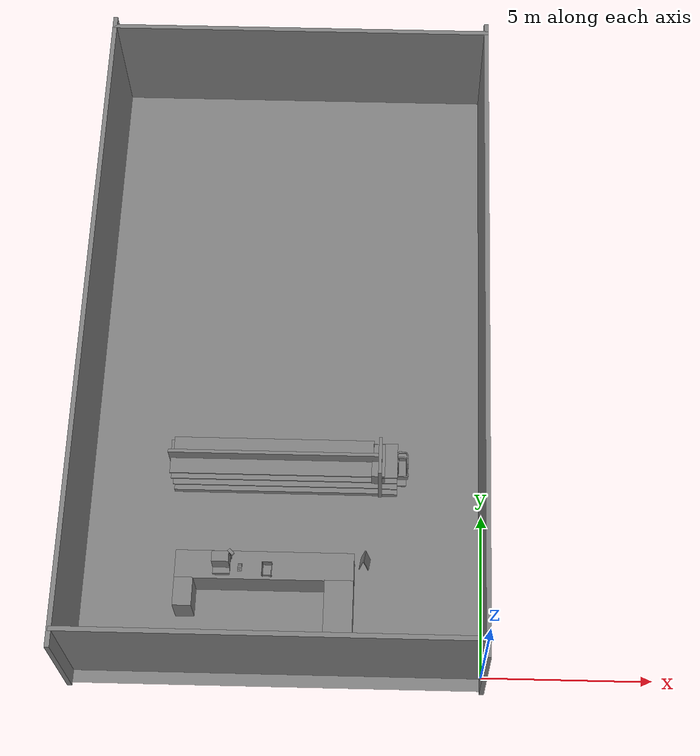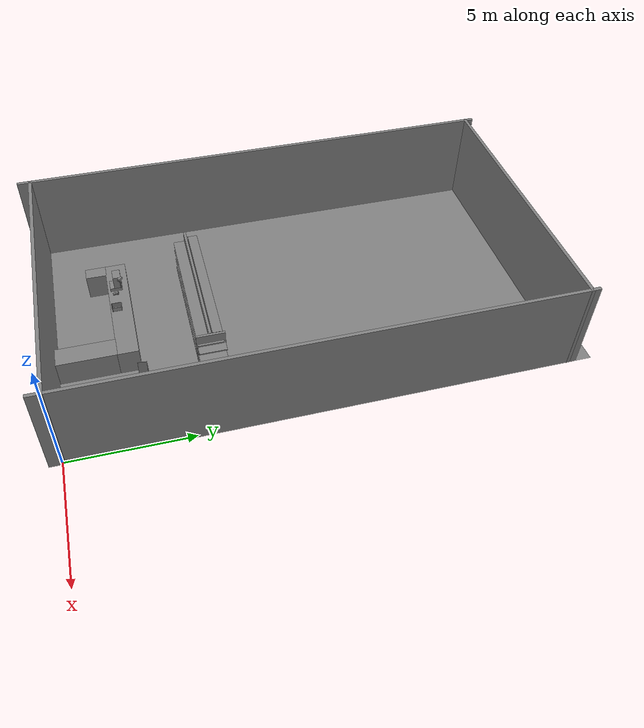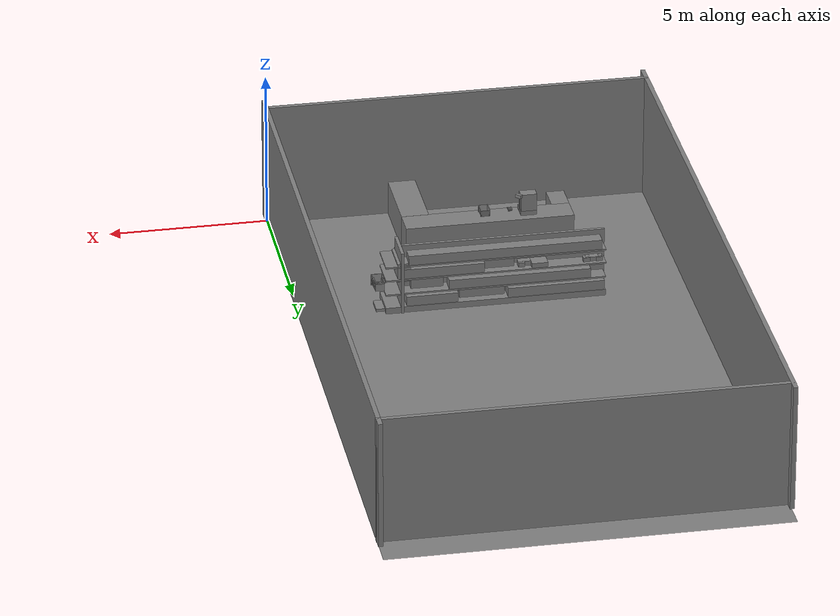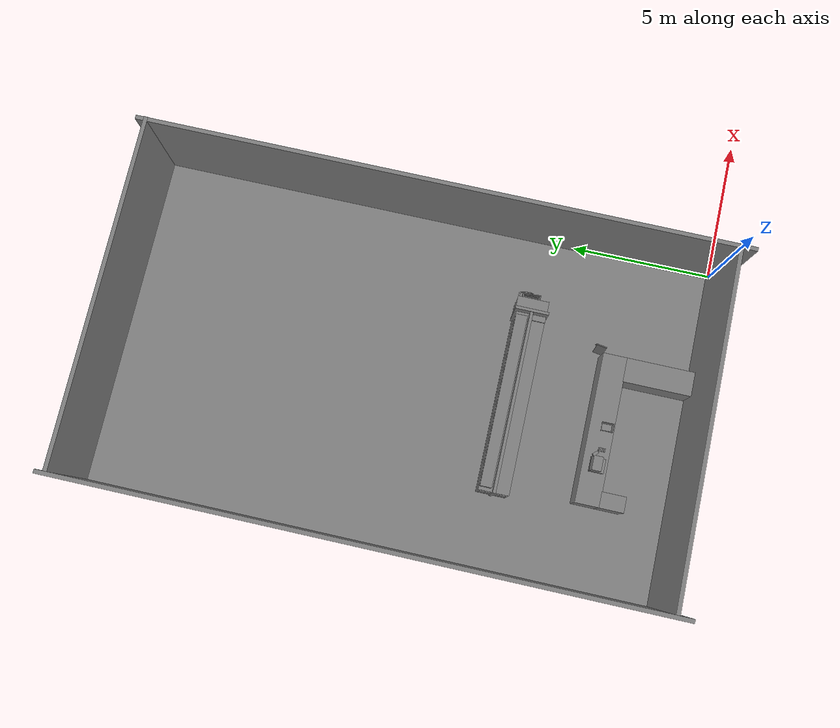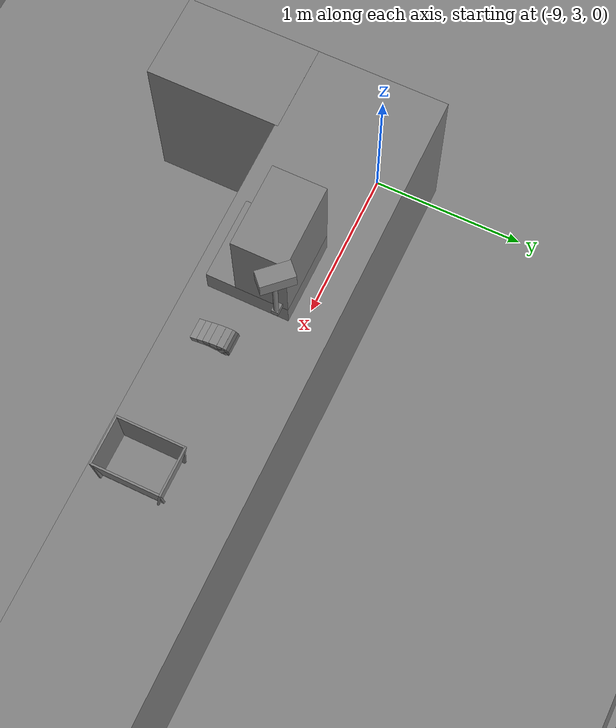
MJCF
<mujoco>
    <option gravity="0.000000000 0.000000000 -9.810000420" timestep="0.0166666" integrator="implicitfast" density="1.225" viscosity="1.8000001e-05" noslip_iterations="10" iterations="100" sdf_iterations="50">
        <flag multiccd="disable"/>
    </option>
    <size memory="1000M"/>
    <compiler coordinate="local"/>
    <worldbody>
        <light cutoff="30" pos="0 1 1" dir="0 -1 -2"/>
        <light cutoff="30" pos="0 -1 1" dir="0 1 -2"/>
        <body pos="-2.436573029 6.404376507 0.137849092" euler="0.000000000 0.000000000 0.000000000" name="openloong_gripper_2f85_fix_base_usda_shoppingtrolley_01">
            <geom contype="1" conaffinity="1" density="1000" type="box" material="" rgba="0.500000000 0.500000000 0.500000000 1.000000000" solimp="0.899999976 0.949999988 0.001000000" friction="1.000000000 0.005000000 0.000100000" solref="0.020000000 1.000000000" margin="0" condim="3" group="0" pos="-0.107458733 0.238907143 0.911498845" quat="0.634576976 0.622505128 -0.330067992 -0.317575932" size="0.017999999 0.022499999 0.035999998" name="openloong_gripper_2f85_fix_base_usda_geom_8E48DE5D_F5A7_4DB1_BB65_A2979D7F157E"/>
            <geom contype="1" conaffinity="1" density="1000" type="box" material="" rgba="0.500000000 0.500000000 0.500000000 1.000000000" solimp="0.899999976 0.949999988 0.001000000" friction="1.000000000 0.005000000 0.000100000" solref="0.020000000 1.000000000" margin="0" condim="3" group="0" pos="-0.126757339 -0.182533979 0.598989725" quat="0.996607184 0.055331606 -0.059003651 -0.015205891" size="0.013499999 0.287999988 0.053999998" name="openloong_gripper_2f85_fix_base_usda_geom_AFE20BA0_E099_486F_BD48_94D25FA9901F"/>
            <geom contype="1" conaffinity="1" density="1000" type="box" material="" rgba="0.500000000 0.500000000 0.500000000 1.000000000" solimp="0.899999976 0.949999988 0.001000000" friction="1.000000000 0.005000000 0.000100000" solref="0.020000000 1.000000000" margin="0" condim="3" group="0" pos="-0.005004787 0.248085022 0.912686050" quat="1.000000000 0.000000000 0.000000000 0.000000000" size="0.107999995 0.022499999 0.022499999" name="openloong_gripper_2f85_fix_base_usda_geom_1C161386_D74D_4F29_BFCD_3948CA8BAD4A"/>
            <geom contype="1" conaffinity="1" density="1000" type="box" material="" rgba="0.500000000 0.500000000 0.500000000 1.000000000" solimp="0.899999976 0.949999988 0.001000000" friction="1.000000000 0.005000000 0.000100000" solref="0.020000000 1.000000000" margin="0" condim="3" group="0" pos="-0.169898406 -0.043119621 0.915120542" quat="0.687021017 0.726584017 -0.005590606 -0.006832919" size="0.017999999 0.022499999 0.089999996" name="openloong_gripper_2f85_fix_base_usda_geom_5F804C67_1E9C_4399_8B1E_7FD52CB1FAF6"/>
            <geom contype="1" conaffinity="1" density="1000" type="box" material="" rgba="0.500000000 0.500000000 0.500000000 1.000000000" solimp="0.899999976 0.949999988 0.001000000" friction="1.000000000 0.005000000 0.000100000" solref="0.020000000 1.000000000" margin="0" condim="3" group="0" pos="0.148195267 -0.199506566 0.782808602" quat="0.998808920 0.017156634 0.026950166 0.036880098" size="0.013499999 0.305999994 0.063000001" name="openloong_gripper_2f85_fix_base_usda_geom_07452491_D3BB_40BF_AED5_DA791EAEF1D9"/>
            <geom contype="1" conaffinity="1" density="1000" type="box" material="" rgba="0.500000000 0.500000000 0.500000000 1.000000000" solimp="0.899999976 0.949999988 0.001000000" friction="1.000000000 0.005000000 0.000100000" solref="0.020000000 1.000000000" margin="0" condim="3" group="0" pos="-0.142927840 -0.199506134 0.784674108" quat="0.998421252 0.016904408 -0.027109101 -0.046199299" size="0.013499999 0.305999994 0.063000001" name="openloong_gripper_2f85_fix_base_usda_geom_1E232036_3E03_4D23_A487_3C4614A84535"/>
            <geom contype="1" conaffinity="1" density="1000" type="box" material="" rgba="0.500000000 0.500000000 0.500000000 1.000000000" solimp="0.899999976 0.949999988 0.001000000" friction="1.000000000 0.005000000 0.000100000" solref="0.020000000 1.000000000" margin="0" condim="3" group="0" pos="-0.000004721 -0.174527690 0.560063601" quat="0.996704638 0.081116498 -0.000000004 0.000000000" size="0.126000002 0.287999988 0.009000000" name="openloong_gripper_2f85_fix_base_usda_geom_6A46088A_E00B_49C9_B678_498374E9230F"/>
            <geom contype="1" conaffinity="1" density="1000" type="box" material="" rgba="0.500000000 0.500000000 0.500000000 1.000000000" solimp="0.899999976 0.949999988 0.001000000" friction="1.000000000 0.005000000 0.000100000" solref="0.020000000 1.000000000" margin="0" condim="3" group="0" pos="-0.160832763 0.103427693 0.910528183" quat="0.711469591 0.699786782 -0.048386075 -0.042050660" size="0.017999999 0.022499999 0.071999997" name="openloong_gripper_2f85_fix_base_usda_geom_78507573_C3D5_42D0_9394_3AA127B2B8FB"/>
            <geom contype="1" conaffinity="1" density="1000" type="box" material="" rgba="0.500000000 0.500000000 0.500000000 1.000000000" solimp="0.899999976 0.949999988 0.001000000" friction="1.000000000 0.005000000 0.000100000" solref="0.020000000 1.000000000" margin="0" condim="3" group="0" pos="-0.169898406 -0.178061336 0.864131629" quat="0.916343808 -0.400392294 -0.000000045 0.000000030" size="0.017999999 0.022499999 0.089999996" name="openloong_gripper_2f85_fix_base_usda_geom_F3EA36E6_692F_418E_AC3F_CC9962546C88"/>
            <geom contype="1" conaffinity="1" density="1000" type="box" material="" rgba="0.500000000 0.500000000 0.500000000 1.000000000" solimp="0.899999976 0.949999988 0.001000000" friction="1.000000000 0.005000000 0.000100000" solref="0.020000000 1.000000000" margin="0" condim="3" group="0" pos="-0.000006008 -0.484932661 0.670727849" quat="0.997585475 0.069449045 -0.000000004 -0.000000089" size="0.179999992 0.013499999 0.170999989" name="openloong_gripper_2f85_fix_base_usda_geom_936D97F6_509F_482E_8645_C0526AAC4270"/>
            <geom contype="1" conaffinity="1" density="1000" type="box" material="" rgba="0.500000000 0.500000000 0.500000000 1.000000000" solimp="0.899999976 0.949999988 0.001000000" friction="1.000000000 0.005000000 0.000100000" solref="0.020000000 1.000000000" margin="0" condim="3" group="0" pos="0.134013891 0.200098798 0.912192523" quat="0.692574680 -0.680924535 -0.166899428 0.169783980" size="0.017999999 0.022499999 0.035999998" name="openloong_gripper_2f85_fix_base_usda_geom_54ED400D_82B2_4020_9F93_DDC1C57F0784"/>
            <geom contype="1" conaffinity="1" density="1000" type="box" material="" rgba="0.500000000 0.500000000 0.500000000 1.000000000" solimp="0.899999976 0.949999988 0.001000000" friction="1.000000000 0.005000000 0.000100000" solref="0.020000000 1.000000000" margin="0" condim="3" group="0" pos="0.141839072 -0.191051379 0.702451229" quat="0.997147262 0.056065105 0.045779929 0.021407485" size="0.013499999 0.287999988 0.053999998" name="openloong_gripper_2f85_fix_base_usda_geom_D29C9CE1_F4CA_4536_8418_E5E96C3CAF4E"/>
            <geom contype="1" conaffinity="1" density="1000" type="box" material="" rgba="0.500000000 0.500000000 0.500000000 1.000000000" solimp="0.899999976 0.949999988 0.001000000" friction="1.000000000 0.005000000 0.000100000" solref="0.020000000 1.000000000" margin="0" condim="3" group="0" pos="0.169898629 -0.178061336 0.864131629" quat="0.916343808 -0.400392294 -0.000000045 0.000000030" size="0.017999999 0.022499999 0.089999996" name="openloong_gripper_2f85_fix_base_usda_geom_FE6E8121_F6AF_4322_ADAE_E070F9635254"/>
            <geom contype="1" conaffinity="1" density="1000" type="box" material="" rgba="0.500000000 0.500000000 0.500000000 1.000000000" solimp="0.899999976 0.949999988 0.001000000" friction="1.000000000 0.005000000 0.000100000" solref="0.020000000 1.000000000" margin="0" condim="3" group="0" pos="-0.000005364 0.100332208 0.734785020" quat="0.999668717 0.025737956 -0.000000010 0.000000000" size="0.135000005 0.019800000 0.152999997" name="openloong_gripper_2f85_fix_base_usda_geom_CC81ECE5_C61E_42DA_AAA3_A25E2C682272"/>
            <geom contype="1" conaffinity="1" density="1000" type="box" material="" rgba="0.500000000 0.500000000 0.500000000 1.000000000" solimp="0.899999976 0.949999988 0.001000000" friction="1.000000000 0.005000000 0.000100000" solref="0.020000000 1.000000000" margin="0" condim="3" group="0" pos="-0.012634277 -0.174527690 -0.088243507" quat="1.000000000 0.000000000 -0.000000004 0.000000000" size="0.135000005 0.287999988 0.044999998" name="openloong_gripper_2f85_fix_base_usda_geom_FA8AE577_57FA_4B66_9606_76C208685E1F"/>
            <geom contype="1" conaffinity="1" density="1000" type="box" material="" rgba="0.500000000 0.500000000 0.500000000 1.000000000" solimp="0.899999976 0.949999988 0.001000000" friction="1.000000000 0.005000000 0.000100000" solref="0.020000000 1.000000000" margin="0" condim="3" group="0" pos="0.131482959 -0.182533979 0.598989725" quat="0.996607125 0.055331629 0.059003670 0.015205893" size="0.013499999 0.287999988 0.053999998" name="openloong_gripper_2f85_fix_base_usda_geom_03648058_B4A2_40A5_8245_5C2EC943771F"/>
            <geom contype="1" conaffinity="1" density="1000" type="box" material="" rgba="0.500000000 0.500000000 0.500000000 1.000000000" solimp="0.899999976 0.949999988 0.001000000" friction="1.000000000 0.005000000 0.000100000" solref="0.020000000 1.000000000" margin="0" condim="3" group="0" pos="0.103667587 0.233050480 0.912927270" quat="0.634205043 -0.622199059 -0.324503720 0.324576139" size="0.017999999 0.022499999 0.035999998" name="openloong_gripper_2f85_fix_base_usda_geom_D37723F8_A622_44B5_9CE7_448D9D5AF1D6"/>
            <geom contype="1" conaffinity="1" density="1000" type="box" material="" rgba="0.500000000 0.500000000 0.500000000 1.000000000" solimp="0.899999976 0.949999988 0.001000000" friction="1.000000000 0.005000000 0.000100000" solref="0.020000000 1.000000000" margin="0" condim="3" group="0" pos="-0.134013891 0.200098798 0.912192523" quat="0.694057047 0.679413557 -0.172947660 -0.163618833" size="0.017999999 0.022499999 0.035999998" name="openloong_gripper_2f85_fix_base_usda_geom_BC667089_B079_41B8_BE75_F9047322924A"/>
            <geom contype="1" conaffinity="1" density="1000" type="box" material="" rgba="0.500000000 0.500000000 0.500000000 1.000000000" solimp="0.899999976 0.949999988 0.001000000" friction="1.000000000 0.005000000 0.000100000" solref="0.020000000 1.000000000" margin="0" condim="3" group="0" pos="-0.135714188 -0.191051379 0.694841146" quat="0.997147322 0.056064609 -0.045779683 -0.021407485" size="0.013499999 0.287999988 0.053999998" name="openloong_gripper_2f85_fix_base_usda_geom_9E9956B1_E16B_4E6C_A7B0_21A2CFA500CA"/>
            <geom contype="1" conaffinity="1" density="1000" type="box" material="" rgba="0.500000000 0.500000000 0.500000000 1.000000000" solimp="0.899999976 0.949999988 0.001000000" friction="1.000000000 0.005000000 0.000100000" solref="0.020000000 1.000000000" margin="0" condim="3" group="0" pos="0.169898629 -0.043119621 0.915120542" quat="0.687029123 -0.726576388 -0.006509603 0.005963952" size="0.017999999 0.022499999 0.089999996" name="openloong_gripper_2f85_fix_base_usda_geom_8F8C9066_8849_4109_93C4_37B803EC0EC5"/>
            <geom contype="1" conaffinity="1" density="1000" type="box" material="" rgba="0.500000000 0.500000000 0.500000000 1.000000000" solimp="0.899999976 0.949999988 0.001000000" friction="1.000000000 0.005000000 0.000100000" solref="0.020000000 1.000000000" margin="0" condim="3" group="0" pos="0.160832971 0.103427693 0.910528183" quat="0.711112797 -0.700149298 -0.042821646 0.047705106" size="0.017999999 0.022499999 0.071999997" name="openloong_gripper_2f85_fix_base_usda_geom_B4B4242B_F1F3_4E99_979E_F895690F5C4A"/>
            <freejoint name="openloong_gripper_2f85_fix_base_usda_shoppingtrolley_01_joint"/>
            <site size="0.005000000 0.005000000 0.005000000" rgba="0.500000000 0.500000000 0.500000000 1.000000000" pos="0.000000000 0.000000000 0.000000000" quat="1.000000000 0.000000000 0.000000000 0.000000000" group="0" type="sphere" name="openloong_gripper_2f85_fix_base_usda_shoppingtrolley_01"/>
        </body>
        <body pos="-7.168000221 2.823999882 1.227496982" euler="-0.283413887 0.056829713 -0.133293241" name="openloong_gripper_2f85_fix_base_usda_Pos">
            <geom contype="1" conaffinity="1" density="1000" type="box" material="" rgba="0.500000000 0.500000000 0.500000000 1.000000000" solimp="0.899999976 0.949999988 0.001000000" friction="1.000000000 0.005000000 0.000100000" solref="0.020000000 1.000000000" margin="0" condim="3" group="0" pos="-0.002278805 0.074524641 -0.004134178" quat="0.315989256 0.948762834 0.000000000 0.000000000" size="0.059999999 0.013000000 0.035000000" name="openloong_gripper_2f85_fix_base_usda_geom_002FB390_DEA7_4B7F_A30A_A24B1130C273"/>
            <geom contype="1" conaffinity="1" density="1000" type="box" material="" rgba="0.500000000 0.500000000 0.500000000 1.000000000" solimp="0.899999976 0.949999988 0.001000000" friction="1.000000000 0.005000000 0.000100000" solref="0.020000000 1.000000000" margin="0" condim="3" group="0" pos="-0.002278805 0.078031301 0.008128285" quat="0.990447283 -0.137893349 -0.000000000 0.000000000" size="0.059999999 0.010000000 0.035000000" name="openloong_gripper_2f85_fix_base_usda_geom_A936995E_AC04_4A7C_A4EF_3BB795AF4E7A"/>
            <geom contype="1" conaffinity="1" density="1000" type="box" material="" rgba="0.500000000 0.500000000 0.500000000 1.000000000" solimp="0.899999976 0.949999988 0.001000000" friction="1.000000000 0.005000000 0.000100000" solref="0.020000000 1.000000000" margin="0" condim="3" group="0" pos="-0.002278805 0.080785275 -0.002596974" quat="0.287325412 -0.957833171 0.000000000 -0.000000000" size="0.059999999 0.013000000 0.035000000" name="openloong_gripper_2f85_fix_base_usda_geom_32B29401_0A80_481E_BF6C_20FB1EAAEB6D"/>
            <geom contype="1" conaffinity="1" density="1000" type="box" material="" rgba="0.500000000 0.500000000 0.500000000 1.000000000" solimp="0.899999976 0.949999988 0.001000000" friction="1.000000000 0.005000000 0.000100000" solref="0.020000000 1.000000000" margin="0" condim="3" group="0" pos="-0.002278805 -0.098804474 -0.020147085" quat="0.988851428 0.148906425 0.000000000 -0.000000000" size="0.059999999 0.022000000 0.020000000" name="openloong_gripper_2f85_fix_base_usda_geom_B8F79BD7_48F1_409D_9F5A_64C1B50F8C2A"/>
            <geom contype="1" conaffinity="1" density="1000" type="box" material="" rgba="0.500000000 0.500000000 0.500000000 1.000000000" solimp="0.899999976 0.949999988 0.001000000" friction="1.000000000 0.005000000 0.000100000" solref="0.020000000 1.000000000" margin="0" condim="3" group="0" pos="-0.002279282 0.019920349 0.012102842" quat="0.995421529 0.095583312 -0.000000000 0.000000000" size="0.059999999 0.025000000 0.026000001" name="openloong_gripper_2f85_fix_base_usda_geom_71BD6544_A571_47AE_A7AE_2B94915A6C56"/>
            <geom contype="1" conaffinity="1" density="1000" type="box" material="" rgba="0.500000000 0.500000000 0.500000000 1.000000000" solimp="0.899999976 0.949999988 0.001000000" friction="1.000000000 0.005000000 0.000100000" solref="0.020000000 1.000000000" margin="0" condim="3" group="0" pos="-0.002279282 0.005734444 -0.014276981" quat="0.999571502 -0.029275293 -0.000000000 0.000000000" size="0.059999999 0.050000001 0.010000000" name="openloong_gripper_2f85_fix_base_usda_geom_CFB93748_3016_458C_B7D9_8BDCC8801B14"/>
            <geom contype="1" conaffinity="1" density="1000" type="box" material="" rgba="0.500000000 0.500000000 0.500000000 1.000000000" solimp="0.899999976 0.949999988 0.001000000" friction="1.000000000 0.005000000 0.000100000" solref="0.020000000 1.000000000" margin="0" condim="3" group="0" pos="-0.002278805 0.079460382 0.007771969" quat="0.922590315 -0.385781497 -0.000000000 0.000000000" size="0.059999999 0.010000000 0.035000000" name="openloong_gripper_2f85_fix_base_usda_geom_34DA81AA_1C08_4FD1_8BE3_EA44C69E73E0"/>
            <geom contype="1" conaffinity="1" density="1000" type="box" material="" rgba="0.500000000 0.500000000 0.500000000 1.000000000" solimp="0.899999976 0.949999988 0.001000000" friction="1.000000000 0.005000000 0.000100000" solref="0.020000000 1.000000000" margin="0" condim="3" group="0" pos="-0.002279282 0.081384182 -0.001320124" quat="0.590483606 -0.807049692 0.000000000 0.000000000" size="0.059999999 0.013000000 0.035000000" name="openloong_gripper_2f85_fix_base_usda_geom_3352D73E_B3E8_47AF_9818_6BD5189BB2F0"/>
            <geom contype="1" conaffinity="1" density="1000" type="box" material="" rgba="0.500000000 0.500000000 0.500000000 1.000000000" solimp="0.899999976 0.949999988 0.001000000" friction="1.000000000 0.005000000 0.000100000" solref="0.020000000 1.000000000" margin="0" condim="3" group="0" pos="-0.002278805 -0.059297562 -0.007972836" quat="0.988851428 0.148906425 0.000000000 -0.000000000" size="0.059999999 0.020000000 0.022000000" name="openloong_gripper_2f85_fix_base_usda_geom_4C96A4E1_DF54_43F3_8C76_EC9801C8DC17"/>
            <geom contype="1" conaffinity="1" density="1000" type="box" material="" rgba="0.500000000 0.500000000 0.500000000 1.000000000" solimp="0.899999976 0.949999988 0.001000000" friction="1.000000000 0.005000000 0.000100000" solref="0.020000000 1.000000000" margin="0" condim="3" group="0" pos="-0.002278805 0.076618671 -0.004656911" quat="0.004634960 0.999989390 -0.000000000 0.000000000" size="0.059999999 0.013000000 0.035000000" name="openloong_gripper_2f85_fix_base_usda_geom_7A34E6A8_32AF_4029_9D84_76798D578BC7"/>
            <geom contype="1" conaffinity="1" density="1000" type="box" material="" rgba="0.500000000 0.500000000 0.500000000 1.000000000" solimp="0.899999976 0.949999988 0.001000000" friction="1.000000000 0.005000000 0.000100000" solref="0.020000000 1.000000000" margin="0" condim="3" group="0" pos="-0.002279282 -0.021952629 0.002959967" quat="0.991270185 0.131847635 0.000000000 -0.000000000" size="0.059999999 0.020000000 0.024000000" name="openloong_gripper_2f85_fix_base_usda_geom_5C5E5142_F718_4D3E_B779_9A8EE55296E2"/>
            <geom contype="1" conaffinity="1" density="1000" type="box" material="" rgba="0.500000000 0.500000000 0.500000000 1.000000000" solimp="0.899999976 0.949999988 0.001000000" friction="1.000000000 0.005000000 0.000100000" solref="0.020000000 1.000000000" margin="0" condim="3" group="0" pos="-0.002278805 0.081418991 0.002587795" quat="0.803492188 -0.595315576 0.000000000 0.000000000" size="0.059999999 0.013000000 0.035000000" name="openloong_gripper_2f85_fix_base_usda_geom_EE9ABFE8_1BC6_4179_89A8_2A41F00E52D6"/>
            <geom contype="1" conaffinity="1" density="1000" type="box" material="" rgba="0.500000000 0.500000000 0.500000000 1.000000000" solimp="0.899999976 0.949999988 0.001000000" friction="1.000000000 0.005000000 0.000100000" solref="0.020000000 1.000000000" margin="0" condim="3" group="0" pos="-0.002278805 0.061115503 0.008545756" quat="0.999325931 0.036714435 -0.000000000 -0.000000000" size="0.059999999 0.020000000 0.035000000" name="openloong_gripper_2f85_fix_base_usda_geom_867B6519_375A_4453_970D_BE975EED43E0"/>
            <freejoint name="openloong_gripper_2f85_fix_base_usda_pos_scan"/>
        </body>
        <body pos="-3.510578632 3.403555870 -0.000000100" euler="0.000000000 0.000000000 40.200675964" name="openloong_gripper_2f85_fix_base_usda_PZ">
            <geom contype="1" conaffinity="1" density="1000" type="box" material="" rgba="0.500000000 0.500000000 0.500000000 1.000000000" solimp="0.899999976 0.949999988 0.001000000" friction="1.000000000 0.005000000 0.000100000" solref="0.020000000 1.000000000" margin="0" condim="3" group="0" pos="-0.047453165 0.056484699 0.373715430" quat="0.934750080 0.077914521 0.028795123 0.345459938" size="0.180000007 0.010000000 0.379999995" name="openloong_gripper_2f85_fix_base_usda_geom_FC08015A_01A1_4DD9_ABC7_54E08C159146"/>
            <geom contype="1" conaffinity="1" density="1000" type="box" material="" rgba="0.500000000 0.500000000 0.500000000 1.000000000" solimp="0.899999976 0.949999988 0.001000000" friction="1.000000000 0.005000000 0.000100000" solref="0.020000000 1.000000000" margin="0" condim="3" group="0" pos="0.047452450 -0.054376602 0.374072611" quat="0.934387863 -0.082143910 -0.030358355 0.345326364" size="0.180000007 0.010000000 0.379999995" name="openloong_gripper_2f85_fix_base_usda_geom_76D7FFA8_7379_4C72_AEAE_A175E23D04A7"/>
            <freejoint name="openloong_gripper_2f85_fix_base_usda_PZ"/>
        </body>
        <body pos="-6.332345009 2.779978037 1.034067392" euler="0.000000000 0.000000000 0.000000000" name="openloong_gripper_2f85_fix_base_usda_basket">
            <geom contype="1" conaffinity="1" density="100000" type="box" material="" rgba="0.500000000 0.500000000 0.500000000 1.000000000" solimp="0.899999976 0.949999988 0.001000000" friction="1.000000000 0.899999976 0.000100000" solref="0.020000000 1.000000000" margin="0" condim="3" group="0" pos="-0.039724827 -0.188568115 0.167089701" quat="0.997537494 0.070135131 0.000000000 0.000000000" size="0.150000006 0.006000000 0.108000003" name="openloong_gripper_2f85_fix_base_usda_geom_29B238C2_3E65_4FBA_BD10_876730CB565A"/>
            <geom contype="1" conaffinity="1" density="100000" type="box" material="" rgba="0.500000000 0.500000000 0.500000000 1.000000000" solimp="0.899999976 0.949999988 0.001000000" friction="1.000000000 0.899999976 0.000100000" solref="0.020000000 1.000000000" margin="0" condim="3" group="0" pos="0.094372749 0.000000000 0.168361664" quat="0.706172049 0.036353335 0.036353379 0.706171215" size="0.200000003 0.006000000 0.108000003" name="openloong_gripper_2f85_fix_base_usda_geom_2A44A35D_FFB2_44B9_934B_920188B3B10A"/>
            <geom contype="1" conaffinity="1" density="100000" type="box" material="" rgba="0.500000000 0.500000000 0.500000000 1.000000000" solimp="0.899999976 0.949999988 0.001000000" friction="1.000000000 0.899999976 0.000100000" solref="0.020000000 1.000000000" margin="0" condim="3" group="0" pos="-0.039724827 0.000000000 0.068126202" quat="1.000000000 0.000000000 0.000000000 0.000000000" size="0.129999995 0.174999997 0.006000000" name="openloong_gripper_2f85_fix_base_usda_geom_155CED89_5967_45BB_B887_B38CFEDB58B1"/>
            <geom contype="1" conaffinity="1" density="100000" type="box" material="" rgba="0.500000000 0.500000000 0.500000000 1.000000000" solimp="0.899999976 0.949999988 0.001000000" friction="1.000000000 0.899999976 0.000100000" solref="0.020000000 1.000000000" margin="0" condim="3" group="0" pos="-0.039724827 0.188377380 0.167089701" quat="0.997489929 -0.070808925 0.000000000 0.000000000" size="0.150000006 0.006000000 0.108000003" name="openloong_gripper_2f85_fix_base_usda_geom_D2D50D6D_B49E_4A3C_84D9_605D2301A622"/>
            <geom contype="1" conaffinity="1" density="100000" type="box" material="" rgba="0.500000000 0.500000000 0.500000000 1.000000000" solimp="0.899999976 0.949999988 0.001000000" friction="1.000000000 0.899999976 0.000100000" solref="0.020000000 1.000000000" margin="0" condim="3" group="0" pos="-0.172339439 0.000000000 0.168361664" quat="0.706172407 -0.036353018 -0.036353093 0.706170976" size="0.200000003 0.006000000 0.108000003" name="openloong_gripper_2f85_fix_base_usda_geom_09C6C322_4BAB_4AC5_952B_C5D78C227367"/>
            <freejoint name="openloong_gripper_2f85_fix_base_usda_basket_joint"/>
            <site size="0.005000000 0.005000000 0.005000000" rgba="0.500000000 0.500000000 0.500000000 1.000000000" pos="0.000000000 0.000000000 0.000000000" quat="1.000000000 0.000000000 0.000000000 0.000000000" group="0" type="sphere" name="openloong_gripper_2f85_fix_base_usda_basketsite"/>
        </body>
        <body pos="0.000000000 0.000000000 0.000000000" euler="0.000000000 0.000000000 0.000000000" name=" Static Objects_ Static Objects">
            <geom contype="1" conaffinity="1" density="1000" type="box" material="" rgba="0.500000000 0.500000000 0.500000000 1.000000000" solimp="0.899999976 0.949999988 0.001000000" friction="1.000000000 0.005000000 0.000100000" solref="0.020000000 1.000000000" margin="0" condim="3" group="0" pos="-6.286010742 6.153595448 1.563861728" quat="0.707107067 0.000000000 0.000000000 0.707106471" size="0.529999971 3.134999990 0.025000000" name=" Static Objects_geom_5E2EA822_8387_43C7_A0EA_861521180043"/>
            <geom contype="1" conaffinity="1" density="1000" type="box" material="" rgba="0.500000000 0.500000000 0.500000000 1.000000000" solimp="0.899999976 0.949999988 0.001000000" friction="1.000000000 0.005000000 0.000100000" solref="0.020000000 1.000000000" margin="0" condim="3" group="0" pos="-3.101639986 6.150595188 1.018643856" quat="1.000000000 0.000000000 0.000000000 0.000000000" size="0.050000001 0.579999983 1.019999981" name=" Static Objects_geom_8123BBC7_2909_4877_9ECF_32B243D49121"/>
            <geom contype="1" conaffinity="1" density="1000" type="box" material="" rgba="0.500000000 0.500000000 0.500000000 1.000000000" solimp="0.899999976 0.949999988 0.001000000" friction="1.000000000 0.005000000 0.000100000" solref="0.020000000 1.000000000" margin="0" condim="3" group="0" pos="-2.825197220 6.153595448 1.563861728" quat="0.707107067 0.000000000 0.000000000 0.707106471" size="0.550000012 0.239999995 0.025000000" name=" Static Objects_geom_4A6D72D2_2ED7_4A8E_8C40_14C2E6DA91B6"/>
            <geom contype="1" conaffinity="1" density="1000" type="box" material="" rgba="0.500000000 0.500000000 0.500000000 1.000000000" solimp="0.899999976 0.949999988 0.001000000" friction="1.000000000 0.005000000 0.000100000" solref="0.020000000 1.000000000" margin="0" condim="3" group="0" pos="-6.311686516 6.153595448 1.018643856" quat="0.707107067 0.000000000 0.000000000 0.707106471" size="0.050000001 3.150000095 1.019999981" name=" Static Objects_geom_71FD6B2F_24B7_407D_82FD_4D65DDD0A7DA"/>
            <geom contype="1" conaffinity="1" density="1000" type="box" material="" rgba="0.500000000 0.500000000 0.500000000 1.000000000" solimp="0.899999976 0.949999988 0.001000000" friction="1.000000000 0.005000000 0.000100000" solref="0.020000000 1.000000000" margin="0" condim="3" group="0" pos="-2.825197220 6.153595448 1.115278244" quat="0.707107067 0.000000000 0.000000000 0.707106471" size="0.550000012 0.239999995 0.025000000" name=" Static Objects_geom_8F285E73_9D06_4BA0_8B8D_6530C9C814C8"/>
            <geom contype="1" conaffinity="1" density="1000" type="box" material="" rgba="0.500000000 0.500000000 0.500000000 1.000000000" solimp="0.899999976 0.949999988 0.001000000" friction="1.000000000 0.005000000 0.000100000" solref="0.020000000 1.000000000" margin="0" condim="3" group="0" pos="-6.293097973 6.153595448 1.114443064" quat="0.707107067 0.000000000 0.000000000 0.707106471" size="0.529999971 3.134999990 0.025000000" name=" Static Objects_geom_BC0A7BB1_BEE8_407A_AFA4_8422C98653BD"/>
            <geom contype="1" conaffinity="1" density="1000" type="box" material="" rgba="0.500000000 0.500000000 0.500000000 1.000000000" solimp="0.899999976 0.949999988 0.001000000" friction="1.000000000 0.005000000 0.000100000" solref="0.020000000 1.000000000" margin="0" condim="3" group="0" pos="-2.825197220 6.153595448 0.629031777" quat="0.707107067 0.000000000 0.000000000 0.707106471" size="0.550000012 0.239999995 0.025000000" name=" Static Objects_geom_7CD3D04F_5DC3_4781_A5B2_7CB49039529D"/>
            <geom contype="1" conaffinity="1" density="1000" type="box" material="" rgba="0.500000000 0.500000000 0.500000000 1.000000000" solimp="0.899999976 0.949999988 0.001000000" friction="1.000000000 0.005000000 0.000100000" solref="0.020000000 1.000000000" margin="0" condim="3" group="0" pos="-6.286010742 6.153595448 0.096129179" quat="0.707107067 0.000000000 0.000000000 0.707106471" size="0.529999971 3.134999990 0.098999999" name=" Static Objects_geom_C9299046_34DD_48D5_9836_C7D7724CA935"/>
            <geom contype="1" conaffinity="1" density="1000" type="box" material="" rgba="0.500000000 0.500000000 0.500000000 1.000000000" solimp="0.899999976 0.949999988 0.001000000" friction="1.000000000 0.005000000 0.000100000" solref="0.020000000 1.000000000" margin="0" condim="3" group="0" pos="-2.825197220 6.153595448 0.097434282" quat="0.707107067 0.000000000 0.000000000 0.707106471" size="0.550000012 0.239999995 0.098999999" name=" Static Objects_geom_A44E80F1_052F_4E02_A79A_F06F3F282690"/>
            <geom contype="1" conaffinity="1" density="1000" type="box" material="" rgba="0.500000000 0.500000000 0.500000000 1.000000000" solimp="0.899999976 0.949999988 0.001000000" friction="1.000000000 0.005000000 0.000100000" solref="0.020000000 1.000000000" margin="0" condim="3" group="0" pos="-6.286010742 6.153595448 0.629031777" quat="0.707107067 0.000000000 0.000000000 0.707106471" size="0.529999971 3.134999990 0.025000000" name=" Static Objects_geom_D3FB9221_9E6E_4AAB_BE4F_E819F7636EDD"/>
            <geom contype="1" conaffinity="1" density="1000" type="box" material="" rgba="0.500000000 0.500000000 0.500000000 1.000000000" solimp="0.899999976 0.949999988 0.001000000" friction="1.000000000 0.005000000 0.000100000" solref="0.020000000 1.000000000" margin="0" condim="3" group="0" pos="-6.000000000 20.159999847 2.000000000" quat="1.000000000 0.000000000 0.000000000 0.000000000" size="6.079999924 0.070000000 2.000000000" name=" Static Objects_geom_09F92951_8839_4194_9749_8FDD8CE415FE"/>
            <geom contype="1" conaffinity="1" density="1000" type="box" material="" rgba="0.500000000 0.500000000 0.500000000 1.000000000" solimp="0.899999976 0.949999988 0.001000000" friction="1.000000000 0.005000000 0.000100000" solref="0.020000000 1.000000000" margin="0" condim="3" group="0" pos="-6.000000000 0.035000000 2.000000000" quat="1.000000000 0.000000000 0.000000000 0.000000000" size="6.079999924 0.070000000 2.000000000" name=" Static Objects_geom_F5D23A45_8C27_4B1D_8CF7_0C24B479A77C"/>
            <geom contype="1" conaffinity="1" density="1000" type="box" material="" rgba="0.500000000 0.500000000 0.500000000 1.000000000" solimp="0.899999976 0.949999988 0.001000000" friction="1.000000000 0.005000000 0.000100000" solref="0.020000000 1.000000000" margin="0" condim="3" group="0" pos="0.000000000 10.000000000 2.000000000" quat="1.000000000 0.000000000 0.000000000 0.000000000" size="0.070000000 10.500000000 2.000000000" name=" Static Objects_geom_5F4B5FF6_5022_43E5_9EA9_D29678B131A2"/>
            <geom contype="1" conaffinity="1" density="1000" type="box" material="" rgba="0.500000000 0.500000000 0.500000000 1.000000000" solimp="0.899999976 0.949999988 0.001000000" friction="1.000000000 0.005000000 0.000100000" solref="0.020000000 1.000000000" margin="0" condim="3" group="0" pos="-12.050000191 10.000000000 2.000000000" quat="1.000000000 0.000000000 0.000000000 0.000000000" size="0.070000000 10.500000000 2.000000000" name=" Static Objects_geom_09567B9A_5DA6_4268_9DF2_8FCE7705663C"/>
            <geom contype="1" conaffinity="1" density="1000" type="plane" material="" rgba="0.500000000 0.500000000 0.500000000 1.000000000" solimp="0.899999976 0.949999988 0.001000000" friction="1.000000000 0.005000000 0.000100000" solref="0.020000000 1.000000000" margin="0" condim="3" group="0" pos="-6.000000000 10.399999619 0.000000000" quat="1.000000000 0.000000000 0.000000000 0.000000000" size="6.050000191 10.800000191 0.010000000" name=" Static Objects_geom_41BECC1C_E396_4DDD_BA6F_88E7887A2785"/>
            <geom contype="1" conaffinity="1" density="1000" type="box" material="" rgba="0.500000000 0.500000000 0.500000000 1.000000000" solimp="0.899999976 0.949999988 0.001000000" friction="1.000000000 0.005000000 0.000100000" solref="0.020000000 1.000000000" margin="0" condim="3" group="0" pos="-8.830721855 2.096410990 0.549305558" quat="1.000000000 0.000000000 0.000000000 0.000000000" size="0.280000001 0.430000007 0.550000012" name=" Static Objects_geom_CA74CF34_1A10_405D_AACA_145C48461609"/>
            <geom contype="1" conaffinity="1" density="1000" type="box" material="" rgba="0.500000000 0.500000000 0.500000000 1.000000000" solimp="0.899999976 0.949999988 0.001000000" friction="1.000000000 0.005000000 0.000100000" solref="0.020000000 1.000000000" margin="0" condim="3" group="0" pos="-6.460197449 2.937205315 0.548931718" quat="1.000000000 0.000000000 0.000000000 0.000000000" size="2.650000095 0.430000007 0.550000012" name=" Static Objects_geom_EE124DEB_00E5_457B_B74A_8AF2216FA714"/>
            <geom contype="1" conaffinity="1" density="1000" type="box" material="" rgba="0.500000000 0.500000000 0.500000000 1.000000000" solimp="0.899999976 0.949999988 0.001000000" friction="1.000000000 0.005000000 0.000100000" solref="0.020000000 1.000000000" margin="0" condim="3" group="0" pos="-4.240264893 1.327049494 0.549888909" quat="1.000000000 0.000000000 0.000000000 0.000000000" size="0.430000007 1.200000048 0.550000012" name=" Static Objects_geom_D285525F_3011_4728_8373_7EA7F3A5D0DF"/>
            <geom contype="1" conaffinity="1" density="1000" type="box" material="" rgba="0.500000000 0.500000000 0.500000000 1.000000000" solimp="0.899999976 0.949999988 0.001000000" friction="1.000000000 0.005000000 0.000100000" solref="0.020000000 1.000000000" margin="0" condim="3" group="0" pos="-7.408766270 3.088089943 1.776644945" quat="0.928051054 0.000000000 0.000000000 0.372453064" size="0.050000001 0.100000001 0.050000001" name=" Static Objects_geom_A6E59588_82EB_440F_9E69_F84F80685198"/>
            <geom contype="1" conaffinity="1" density="1000" type="box" material="" rgba="0.500000000 0.500000000 0.500000000 1.000000000" solimp="0.899999976 0.949999988 0.001000000" friction="1.000000000 0.005000000 0.000100000" solref="0.020000000 1.000000000" margin="0" condim="3" group="0" pos="-7.437745571 3.067511320 1.289965630" quat="1.000000000 0.000000000 0.000000000 0.000000000" size="0.029999999 0.020000000 0.020000000" name=" Static Objects_geom_4513689A_3639_4330_A735_9CFBAE067DF7"/>
            <geom contype="1" conaffinity="1" density="1000" type="box" material="" rgba="0.500000000 0.500000000 0.500000000 1.000000000" solimp="0.899999976 0.949999988 0.001000000" friction="1.000000000 0.005000000 0.000100000" solref="0.020000000 1.000000000" margin="0" condim="3" group="0" pos="-7.719123363 2.867671013 1.173410416" quat="1.000000000 0.000000000 0.000000000 0.000000000" size="0.250000000 0.250000000 0.079999998" name=" Static Objects_geom_6AE5588D_A83F_4E3C_B570_9C26F00C9C09"/>
            <geom contype="1" conaffinity="1" density="1000" type="box" material="" rgba="0.500000000 0.500000000 0.500000000 1.000000000" solimp="0.899999976 0.949999988 0.001000000" friction="1.000000000 0.005000000 0.000100000" solref="0.020000000 1.000000000" margin="0" condim="3" group="0" pos="-7.719123363 2.958004713 1.530241251" quat="1.000000000 0.000000000 0.000000000 0.000000000" size="0.250000000 0.159999996 0.280000001" name=" Static Objects_geom_D007814B_F4BA_4D40_8249_EFA9AAE53DAB"/>
            <geom contype="1" conaffinity="1" density="1000" type="cylinder" material="" rgba="0.500000000 0.500000000 0.500000000 1.000000000" solimp="0.899999976 0.949999988 0.001000000" friction="1.000000000 0.005000000 0.000100000" solref="0.020000000 1.000000000" margin="0" condim="3" group="0" pos="-7.427312374 3.069516420 1.502544641" quat="0.928051054 0.000000000 0.000000000 0.372453064" size="0.015000000 0.230000004 0.100000001" name=" Static Objects_geom_605E1C13_70CE_4DE8_9358_1979A5CA8C2A"/>
            <geom contype="1" conaffinity="1" density="1000" type="box" material="" rgba="0.500000000 0.500000000 0.500000000 1.000000000" solimp="0.899999976 0.949999988 0.001000000" friction="1.000000000 0.005000000 0.000100000" solref="0.020000000 1.000000000" margin="0" condim="3" group="0" pos="-9.058088303 6.434794426 1.209077358" quat="1.000000000 0.000000000 0.000000000 0.000000000" size="0.250000000 0.100000001 0.070000000" name=" Static Objects_geom_0F62FCA6_0575_40DD_A63F_90A9AC8F3903"/>
            <geom contype="1" conaffinity="1" density="1000" type="box" material="" rgba="0.500000000 0.500000000 0.500000000 1.000000000" solimp="0.899999976 0.949999988 0.001000000" friction="1.000000000 0.005000000 0.000100000" solref="0.020000000 1.000000000" margin="0" condim="3" group="0" pos="-5.611940861 6.318420410 0.350975692" quat="1.000000000 0.000000000 0.000000000 0.000000000" size="0.699999988 0.100000001 0.150000006" name=" Static Objects_geom_641820D5_DE62_463C_AF1F_5FA83D6EA658"/>
            <geom contype="1" conaffinity="1" density="1000" type="box" material="" rgba="0.500000000 0.500000000 0.500000000 1.000000000" solimp="0.899999976 0.949999988 0.001000000" friction="1.000000000 0.005000000 0.000100000" solref="0.020000000 1.000000000" margin="0" condim="3" group="0" pos="-9.237723351 6.464855671 1.209077358" quat="1.000000000 0.000000000 0.000000000 0.000000000" size="0.100000001 0.100000001 0.070000000" name=" Static Objects_geom_56D16765_02AF_427F_BA92_682F6959F631"/>
            <geom contype="1" conaffinity="1" density="1000" type="box" material="" rgba="0.500000000 0.500000000 0.500000000 1.000000000" solimp="0.899999976 0.949999988 0.001000000" friction="1.000000000 0.005000000 0.000100000" solref="0.020000000 1.000000000" margin="0" condim="3" group="0" pos="-6.300771236 6.459744930 1.744376063" quat="1.000000000 0.000000000 0.000000000 0.000000000" size="3.000000000 0.200000003 0.150000006" name=" Static Objects_geom_CB7C857C_3D22_47FE_91AB_3D508F35FB3B"/>
            <geom contype="1" conaffinity="1" density="1000" type="box" material="" rgba="0.500000000 0.500000000 0.500000000 1.000000000" solimp="0.899999976 0.949999988 0.001000000" friction="1.000000000 0.005000000 0.000100000" solref="0.020000000 1.000000000" margin="0" condim="3" group="0" pos="-7.373087406 6.458900928 1.214329123" quat="1.000000000 0.000000000 0.000000000 0.000000000" size="0.250000000 0.200000003 0.075000003" name=" Static Objects_geom_570FE461_188F_4322_8D24_FF2A11CECBE8"/>
            <geom contype="1" conaffinity="1" density="1000" type="box" material="" rgba="0.500000000 0.500000000 0.500000000 1.000000000" solimp="0.899999976 0.949999988 0.001000000" friction="1.000000000 0.005000000 0.000100000" solref="0.020000000 1.000000000" margin="0" condim="3" group="0" pos="-4.035642624 6.459744930 0.352518857" quat="1.000000000 0.000000000 0.000000000 0.000000000" size="0.800000012 0.200000003 0.150000006" name=" Static Objects_geom_ABCC4613_D743_4858_BAAA_FEB3DDD807A8"/>
            <geom contype="1" conaffinity="1" density="1000" type="box" material="" rgba="0.500000000 0.500000000 0.500000000 1.000000000" solimp="0.899999976 0.949999988 0.001000000" friction="1.000000000 0.005000000 0.000100000" solref="0.020000000 1.000000000" margin="0" condim="3" group="0" pos="-3.907610416 6.318625927 0.800981164" quat="1.000000000 0.000000000 0.000000000 0.000000000" size="0.500000000 0.100000001 0.150000006" name=" Static Objects_geom_D11EE302_DB4A_4161_9FB6_5ADCD6AA20FF"/>
            <geom contype="1" conaffinity="1" density="1000" type="box" material="" rgba="0.500000000 0.500000000 0.500000000 1.000000000" solimp="0.899999976 0.949999988 0.001000000" friction="1.000000000 0.005000000 0.000100000" solref="0.020000000 1.000000000" margin="0" condim="3" group="0" pos="-6.098561764 6.327973843 1.292199373" quat="1.000000000 0.000000000 0.000000000 0.000000000" size="0.500000000 0.100000001 0.150000006" name=" Static Objects_geom_619E9E5E_2958_4D49_B3B2_73B77F909EDC"/>
            <geom contype="1" conaffinity="1" density="1000" type="box" material="" rgba="0.500000000 0.500000000 0.500000000 1.000000000" solimp="0.899999976 0.949999988 0.001000000" friction="1.000000000 0.005000000 0.000100000" solref="0.020000000 1.000000000" margin="0" condim="3" group="0" pos="-7.886891365 6.459744930 0.352518857" quat="1.000000000 0.000000000 0.000000000 0.000000000" size="1.500000000 0.200000003 0.150000006" name=" Static Objects_geom_610DDAB4_946E_4E96_AD70_39863D8266CB"/>
            <geom contype="1" conaffinity="1" density="1000" type="box" material="" rgba="0.500000000 0.500000000 0.500000000 1.000000000" solimp="0.899999976 0.949999988 0.001000000" friction="1.000000000 0.005000000 0.000100000" solref="0.020000000 1.000000000" margin="0" condim="3" group="0" pos="-6.824534416 6.447464466 1.212718010" quat="1.000000000 0.000000000 0.000000000 0.000000000" size="0.100000001 0.100000001 0.075000003" name=" Static Objects_geom_5C43815D_3072_4E43_AE65_53520F4168F9"/>
            <geom contype="1" conaffinity="1" density="1000" type="box" material="" rgba="0.500000000 0.500000000 0.500000000 1.000000000" solimp="0.899999976 0.949999988 0.001000000" friction="1.000000000 0.005000000 0.000100000" solref="0.020000000 1.000000000" margin="0" condim="3" group="0" pos="-4.407354832 6.459744930 1.292199373" quat="1.000000000 0.000000000 0.000000000 0.000000000" size="1.240000010 0.200000003 0.150000006" name=" Static Objects_geom_C2EE0DD7_1A30_4968_A5B8_7FEEBEF4466F"/>
            <geom contype="1" conaffinity="1" density="1000" type="box" material="" rgba="0.500000000 0.500000000 0.500000000 1.000000000" solimp="0.899999976 0.949999988 0.001000000" friction="1.000000000 0.005000000 0.000100000" solref="0.020000000 1.000000000" margin="0" condim="3" group="0" pos="-6.751636982 6.459744930 0.800981164" quat="1.000000000 0.000000000 0.000000000 0.000000000" size="2.200000048 0.200000003 0.150000006" name=" Static Objects_geom_B11C5B84_6519_4298_B83B_0908204416FD"/>
            <geom contype="1" conaffinity="1" density="1000" type="box" material="" rgba="0.500000000 0.500000000 0.500000000 1.000000000" solimp="0.899999976 0.949999988 0.001000000" friction="1.000000000 0.005000000 0.000100000" solref="0.020000000 1.000000000" margin="0" condim="3" group="0" pos="-6.924745083 6.362090111 1.214329123" quat="1.000000000 0.000000000 0.000000000 0.000000000" size="0.200000003 0.100000001 0.075000003" name=" Static Objects_geom_405D09EC_C254_4303_BED6_159F21CD8B38"/>
            <geom contype="1" conaffinity="1" density="1000" type="box" material="" rgba="0.500000000 0.500000000 0.500000000 1.000000000" solimp="0.899999976 0.949999988 0.001000000" friction="1.000000000 0.005000000 0.000100000" solref="0.020000000 1.000000000" margin="0" condim="3" group="0" pos="-8.844120979 6.464855671 1.209077358" quat="1.000000000 0.000000000 0.000000000 0.000000000" size="0.100000001 0.100000001 0.070000000" name=" Static Objects_geom_F107B8C2_A42A_4EF1_B92F_CBE0CCDCA148"/>
            <geom contype="1" conaffinity="1" density="1000" type="box" material="" rgba="0.500000000 0.500000000 0.500000000 1.000000000" solimp="0.899999976 0.949999988 0.001000000" friction="1.000000000 0.005000000 0.000100000" solref="0.020000000 1.000000000" margin="0" condim="3" group="0" pos="-3.157672644 6.136868477 1.348373055" quat="1.000000000 0.000000000 0.000000000 0.000000000" size="0.200000003 0.519999981 0.300000012" name=" Static Objects_geom_B0D789AF_C778_4A11_A7FA_38DC4A0A3D78"/>
        </body>
        <body pos="0.000000000 0.000000000 0.000000000" euler="0.000000000 0.000000000 0.000000000" name="Interactive Objects_Interactive Objects"/>
        <body pos="-2.162922621 6.180304527 -0.123990871" euler="0.000000000 0.000000000 180.000000000" mocap="true" name="openloong_gripper_2f85_fix_base_usda_leftHandMocap"/>
        <body pos="-2.162922621 6.180304527 -0.123990871" euler="0.000000000 0.000000000 180.000000000" mocap="true" name="openloong_gripper_2f85_fix_base_usda_rightHandMocap"/>
        <body pos="-2.162922621 6.180304527 1.076009154" euler="0.000000000 0.000000000 180.000000000" name="openloong_gripper_2f85_fix_base_usda_base_link">
            <geom contype="1" conaffinity="1" density="1000" type="mesh" material="" rgba="0.783999979 0.783999979 0.783999979 1.000000000" solimp="0.899999976 0.949999988 0.001000000" friction="1.000000000 0.005000000 0.000100000" solref="0.020000000 1.000000000" margin="0" condim="3" group="3" mesh="base_link" pos="0.000000000 0.000000000 0.000000000" quat="1.000000000 0.000000000 0.000000000 0.000000000" size="1.000000000 1.000000000 1.000000000" name="openloong_gripper_2f85_fix_base_usda__geom_7_69BD037C_F4D7_45AC_9FAD_FF218C0C30CC"/>
            <site size="0.005000000 0.005000000 0.005000000" rgba="0.500000000 0.500000000 0.500000000 1.000000000" pos="0.000000000 0.000000000 0.000000000" quat="1.000000000 0.000000000 0.000000000 0.000000000" group="0" type="sphere" name="openloong_gripper_2f85_fix_base_usda_imu"/>
            <inertial mass="22.447001" pos="-0.005664100 -0.001336700 0.238289997" diaginertia="0.374352545 0.277180195 0.220617250" quat="0.999247074 0.035235517 -0.015086859 0.006023135"/>
            <body pos="0.000000000 0.000000000 0.300000072" euler="0.000000000 0.000000000 0.000000000" name="openloong_gripper_2f85_fix_base_usda_dummy_body">
                <geom contype="1" conaffinity="1" density="1000" type="sphere" material="" rgba="0.783999979 0.783999979 0.783999979 1.000000000" solimp="0.899999976 0.949999988 0.001000000" friction="1.000000000 0.005000000 0.000100000" solref="0.020000000 1.000000000" margin="0" condim="3" group="3" pos="0.000000000 0.000000000 0.000000000" quat="1.000000000 0.000000000 0.000000000 0.000000000" size="0.010000000 0.000000000 0.000000000" name="openloong_gripper_2f85_fix_base_usda__geom_8_1715546B_5D05_404E_B3A3_F76C96BB97FC"/>
                <joint armature="0.0099999998" stiffness="0" damping="0.1" axis="0.000000 0.000000 1.000000" type="hinge" name="openloong_gripper_2f85_fix_base_usda_dummy_joint"/>
                <site size="0.010000000 0.005000000 0.005000000" rgba="0.500000000 0.500000000 0.500000000 1.000000000" pos="0.000000000 0.000000000 0.000000000" quat="1.000000000 0.000000000 0.000000000 0.000000000" group="3" type="sphere" name="openloong_gripper_2f85_fix_base_usda_dummy_site"/>
            </body>
            <body pos="0.009000063 0.000000000 0.406399965" euler="0.000000000 0.000000000 0.000000000" name="openloong_gripper_2f85_fix_base_usda_Link_head_yaw">
                <geom contype="1" conaffinity="1" density="1000" type="mesh" material="" rgba="0.783999979 0.783999979 0.783999979 1.000000000" solimp="0.899999976 0.949999988 0.001000000" friction="1.000000000 0.005000000 0.000100000" solref="0.020000000 1.000000000" margin="0" condim="3" group="3" mesh="Link_head_yaw" pos="0.000000000 0.000000000 0.000000000" quat="1.000000000 0.000000000 0.000000000 0.000000000" size="1.000000000 1.000000000 1.000000000" name="openloong_gripper_2f85_fix_base_usda__geom_10_C7F836C5_BC1E_49C8_90C8_C84C860E9F21"/>
                <inertial mass="0.84249002" pos="0.000000000 -0.002081400 0.044801001" diaginertia="0.000700588 0.000629000 0.000553812" quat="0.706933022 -0.015675601 0.015677100 0.706933022"/>
                <body pos="0.000000000 -0.034599781 0.048499942" euler="0.000000000 0.000000000 0.000000000" name="openloong_gripper_2f85_fix_base_usda_Link_head_pitch">
                    <geom contype="1" conaffinity="1" density="1000" type="mesh" material="" rgba="0.783999979 0.783999979 0.783999979 1.000000000" solimp="0.899999976 0.949999988 0.001000000" friction="1.000000000 0.005000000 0.000100000" solref="0.020000000 1.000000000" margin="0" condim="3" group="3" mesh="Link_head_pitch" pos="0.000000000 0.000000000 0.000000000" quat="1.000000000 0.000000000 0.000000000 0.000000000" size="1.000000000 1.000000000 1.000000000" name="openloong_gripper_2f85_fix_base_usda__geom_12_BFB59F85_39D6_4E8C_BFD8_F85346391151"/>
                    <inertial mass="1.3943" pos="0.020569000 0.033004001 0.125000000" diaginertia="0.006381400 0.006289940 0.004481460" quat="0.973390222 0.008406822 0.228157058 0.019624906"/>
                    <body pos="0.000000000 0.030000210 0.000000000" euler="0.000000000 0.000000000 0.000000000" name="openloong_gripper_2f85_fix_base_usda_neck_center_body">
                        <site size="0.010000000 0.005000000 0.005000000" rgba="0.500000000 0.500000000 0.500000000 1.000000000" pos="0.000000000 0.000000000 0.000000000" quat="1.000000000 0.000000000 0.000000000 0.000000000" group="3" type="sphere" name="openloong_gripper_2f85_fix_base_usda_neck_center_site"/>
                        <body pos="0.019999981 0.000000000 0.149999976" euler="-0.000002229 39.998176575 -90.000205994" name="openloong_gripper_2f85_fix_base_usda_camera_head">
                            <site size="0.010000000 0.005000000 0.005000000" rgba="0.500000000 0.500000000 0.500000000 1.000000000" pos="0.000000000 0.000000000 0.000000000" quat="1.000000000 0.000000000 0.000000000 0.000000000" group="3" type="sphere" name="openloong_gripper_2f85_fix_base_usda_camera_head_site"/>
                        </body>
                    </body>
                </body>
            </body>
            <body pos="0.003999949 -0.161600113 0.392199993" euler="0.000000000 0.000000000 0.000000000" name="openloong_gripper_2f85_fix_base_usda_Link_arm_r_01">
                <geom contype="1" conaffinity="1" density="1000" type="mesh" material="" rgba="0.783999979 0.783999979 0.783999979 1.000000000" solimp="0.899999976 0.949999988 0.001000000" friction="1.000000000 0.005000000 0.000100000" solref="0.020000000 1.000000000" margin="0" condim="3" group="3" mesh="Link_arm_r_01" pos="0.000000000 0.000000000 0.000000000" quat="1.000000000 0.000000000 0.000000000 0.000000000" size="1.000000000 1.000000000 1.000000000" name="openloong_gripper_2f85_fix_base_usda__geom_14_32B0B337_F3EE_43F2_8265_51C3DC0BA2C6"/>
                <joint armature="0.0099999998" stiffness="0" damping="1" axis="0.000000 -1.000000 0.000000" limited="true" range="-170.000015259 170.000015259" type="hinge" name="openloong_gripper_2f85_fix_base_usda_J_arm_r_01"/>
                <inertial mass="0.75641" pos="0.004494600 -0.038293999 -0.000001874" diaginertia="0.000842990 0.000803050 0.000587120" quat="-0.000163502 0.707098067 0.000812463 0.707115054"/>
                <body pos="-0.042000055 -0.040999889 0.000000000" euler="0.000000000 0.000000000 0.000000000" name="openloong_gripper_2f85_fix_base_usda_Link_arm_r_02">
                    <geom contype="1" conaffinity="1" density="1000" type="mesh" material="" rgba="0.783999979 0.783999979 0.783999979 1.000000000" solimp="0.899999976 0.949999988 0.001000000" friction="1.000000000 0.005000000 0.000100000" solref="0.020000000 1.000000000" margin="0" condim="3" group="3" mesh="Link_arm_r_02" pos="0.000000000 0.000000000 0.000000000" quat="1.000000000 0.000000000 0.000000000 0.000000000" size="1.000000000 1.000000000 1.000000000" name="openloong_gripper_2f85_fix_base_usda__geom_16_589CE50C_40DE_4DFF_8303_F09D1BEB137D"/>
                    <joint armature="0.0099999998" stiffness="0" damping="1" axis="-1.000000 0.000000 0.000000" limited="true" range="-105.000244141 105.000244141" type="hinge" name="openloong_gripper_2f85_fix_base_usda_J_arm_r_02"/>
                    <inertial mass="0.98500001" pos="0.041999999 -0.067430697 0.000000000" diaginertia="0.002262690 0.001730990 0.001154020" quat="0.500000000 0.500000000 -0.500000000 0.500000000"/>
                    <body pos="0.042000055 -0.122600079 0.000000000" euler="0.000000000 0.000000000 0.000000000" name="openloong_gripper_2f85_fix_base_usda_Link_arm_r_03">
                        <geom contype="1" conaffinity="1" density="1000" type="mesh" material="" rgba="0.783999979 0.783999979 0.783999979 1.000000000" solimp="0.899999976 0.949999988 0.001000000" friction="1.000000000 0.005000000 0.000100000" solref="0.020000000 1.000000000" margin="0" condim="3" group="3" mesh="Link_arm_r_03" pos="0.000000000 0.000000000 0.000000000" quat="1.000000000 0.000000000 0.000000000 0.000000000" size="1.000000000 1.000000000 1.000000000" name="openloong_gripper_2f85_fix_base_usda__geom_18_5A4A1B6E_A638_4F2F_9CAA_BCE8D92A7090"/>
                        <joint armature="0.0099999998" stiffness="0" damping="1" axis="0.000000 -1.000000 0.000000" limited="true" range="-170.000015259 170.000015259" type="hinge" name="openloong_gripper_2f85_fix_base_usda_J_arm_r_03"/>
                        <inertial mass="0.95899999" pos="-0.001413580 -0.164663002 0.020757901" diaginertia="0.002101340 0.002064590 0.000754802" quat="0.560480952 0.454391927 -0.443732947 0.531497955"/>
                        <body pos="0.035300016 -0.177400112 0.024000049" euler="0.000000000 0.000000000 0.000000000" name="openloong_gripper_2f85_fix_base_usda_Link_arm_r_04">
                            <geom contype="1" conaffinity="1" density="1000" type="mesh" material="" rgba="0.783999979 0.783999979 0.783999979 1.000000000" solimp="0.899999976 0.949999988 0.001000000" friction="1.000000000 0.005000000 0.000100000" solref="0.020000000 1.000000000" margin="0" condim="3" group="3" mesh="Link_arm_r_04" pos="0.000000000 0.000000000 0.000000000" quat="1.000000000 0.000000000 0.000000000 0.000000000" size="1.000000000 1.000000000 1.000000000" name="openloong_gripper_2f85_fix_base_usda__geom_20_36F82A84_96BC_4C61_B217_6426538F978B"/>
                            <joint armature="0.0099999998" stiffness="0" damping="1" axis="-1.000000 0.000000 0.000000" limited="true" range="0.000000000 170.000015259" type="hinge" name="openloong_gripper_2f85_fix_base_usda_J_arm_r_04"/>
                            <inertial mass="0.60000002" pos="-0.038727000 -0.060766999 -0.021003000" diaginertia="0.001092610 0.000712422 0.000645102" quat="0.327701002 0.632602990 -0.467366993 0.523443997"/>
                            <body pos="-0.035300016 -0.103499889 -0.024000049" euler="0.000000000 0.000000000 0.000000000" name="openloong_gripper_2f85_fix_base_usda_Link_arm_r_05">
                                <geom contype="1" conaffinity="1" density="1000" type="mesh" material="" rgba="0.783999979 0.783999979 0.783999979 1.000000000" solimp="0.899999976 0.949999988 0.001000000" friction="1.000000000 0.005000000 0.000100000" solref="0.020000000 1.000000000" margin="0" condim="3" group="3" mesh="Link_arm_r_05" pos="0.000000000 0.000000000 0.000000000" quat="1.000000000 0.000000000 0.000000000 0.000000000" size="1.000000000 1.000000000 1.000000000" name="openloong_gripper_2f85_fix_base_usda__geom_22_9A379B06_ABC7_4972_8D87_0C69401C05C1"/>
                                <joint armature="0.0099999998" stiffness="0" damping="1" axis="0.000000 -1.000000 0.000000" limited="true" range="-170.000015259 170.000015259" type="hinge" name="openloong_gripper_2f85_fix_base_usda_J_arm_r_05"/>
                                <inertial mass="0.68976003" pos="0.000032712 -0.068658002 -0.000111780" diaginertia="0.002522510 0.002411100 0.000448695" quat="0.707660973 0.706543028 -0.002603360 0.002470550"/>
                                <body pos="-0.026499987 -0.196499825 0.000000000" euler="0.000000000 0.000000000 0.000000000" name="openloong_gripper_2f85_fix_base_usda_Link_arm_r_06">
                                    <geom contype="1" conaffinity="1" density="1000" type="mesh" material="" rgba="0.783999979 0.783999979 0.783999979 1.000000000" solimp="0.899999976 0.949999988 0.001000000" friction="1.000000000 0.005000000 0.000100000" solref="0.020000000 1.000000000" margin="0" condim="3" group="3" mesh="Link_arm_r_06" pos="0.000000000 0.000000000 0.000000000" quat="1.000000000 0.000000000 0.000000000 0.000000000" size="1.000000000 1.000000000 1.000000000" name="openloong_gripper_2f85_fix_base_usda__geom_24_0FC54B48_CD85_40A4_ADFB_79BB06D0C496"/>
                                    <joint armature="0.0099999998" stiffness="0" damping="1" axis="1.000000 0.000000 0.000000" limited="true" range="-105.000244141 105.000244141" type="hinge" name="openloong_gripper_2f85_fix_base_usda_J_arm_r_06"/>
                                    <inertial mass="0.28" pos="0.026078001 -0.000000896 0.001663700" diaginertia="0.000156930 0.000145601 0.000104979" quat="0.707080841 0.001851080 0.001883810 0.707127810"/>
                                    <body pos="0.026499987 0.000000000 0.031800032" euler="0.000000000 0.000000000 0.000000000" name="openloong_gripper_2f85_fix_base_usda_Link_arm_r_07">
                                        <geom contype="1" conaffinity="1" density="1000" type="mesh" material="" rgba="0.783999979 0.783999979 0.783999979 1.000000000" solimp="0.899999976 0.949999988 0.001000000" friction="1.000000000 0.005000000 0.000100000" solref="0.020000000 1.000000000" margin="0" condim="3" group="3" mesh="Link_arm_r_07" pos="0.000000000 0.000000000 0.000000000" quat="1.000000000 0.000000000 0.000000000 0.000000000" size="1.000000000 1.000000000 1.000000000" name="openloong_gripper_2f85_fix_base_usda__geom_26_F730B8D4_A448_4F6D_BFB0_21B2AD0FF119"/>
                                        <joint armature="0.0099999998" stiffness="0" damping="1" axis="0.000000 0.000000 1.000000" limited="true" range="-60.000133514 60.000133514" type="hinge" name="openloong_gripper_2f85_fix_base_usda_J_arm_r_07"/>
                                        <inertial mass="0.61353999" pos="-0.007859000 -0.158170000 -0.027736001" diaginertia="0.003037610 0.002570910 0.000729379" quat="0.427542925 0.443532884 -0.553093910 0.560867906"/>
                                        <body pos="0.000000000 0.287000179 -0.269999981" euler="150.000350952 0.000000000 0.000000000" name="openloong_gripper_2f85_fix_base_usda_camera_wrist_r">
                                            <site size="0.010000000 0.005000000 0.005000000" rgba="0.500000000 0.500000000 0.500000000 1.000000000" pos="0.000000000 0.000000000 0.000000000" quat="1.000000000 0.000000000 0.000000000 0.000000000" group="3" type="sphere" name="openloong_gripper_2f85_fix_base_usda_camera_wrist_r_site"/>
                                        </body>
                                        <body pos="0.000000000 -0.219999790 -0.032999992" euler="0.000000000 0.000000000 179.999969482" name="openloong_gripper_2f85_fix_base_usda_ee_center_body_r">
                                            <site size="0.010000000 0.005000000 0.005000000" rgba="0.500000000 0.500000000 0.500000000 1.000000000" pos="0.000000000 0.000000000 0.000000000" quat="1.000000000 0.000000000 0.000000000 0.000000000" group="3" type="sphere" name="openloong_gripper_2f85_fix_base_usda_ee_center_site_r"/>
                                        </body>
                                        <body pos="0.000000000 -0.065999985 -0.031000018" euler="89.999984741 0.000000000 180.000000000" name="openloong_gripper_2f85_fix_base_usda_zbr_base_link">
                                            <geom contype="1" conaffinity="1" density="1000" type="mesh" material="" rgba="0.783999979 0.783999979 0.783999979 1.000000000" solimp="0.899999976 0.949999988 0.001000000" friction="1.000000000 0.005000000 0.000100000" solref="0.020000000 1.000000000" margin="0" condim="3" group="3" mesh="base" pos="0.000000000 0.000000000 0.000000000" quat="1.000000000 0.000000000 0.000000000 0.000000000" size="1.000000238 1.000000238 1.000000238" name="openloong_gripper_2f85_fix_base_usda__geom_30_6E544097_EA09_445A_8E57_CB7A9A5A199C"/>
                                            <inertial mass="0.77744102" pos="0.000000000 -0.000027039 0.035467502" diaginertia="0.000260285 0.000225381 0.000152708" quat="0.999998808 -0.001528488 0.000000000 0.000000000"/>
                                            <body pos="-0.030601032 0.004750133 0.065703884" euler="-89.999977112 0.000000000 0.000000000" name="openloong_gripper_2f85_fix_base_usda_r_left_driver">
                                                <geom contype="1" conaffinity="1" density="1000" type="mesh" material="" rgba="0.783999979 0.783999979 0.783999979 1.000000000" solimp="0.899999976 0.949999988 0.001000000" friction="1.000000000 0.005000000 0.000100000" solref="0.020000000 1.000000000" margin="0" condim="3" group="3" mesh="driver" pos="0.030601032 0.054904476 -0.004699946" quat="0.707106709 0.707106590 0.000000000 0.000000000" size="1.000000238 1.000000238 1.000000238" name="openloong_gripper_2f85_fix_base_usda__geom_32_6DBE7E76_4608_4F2A_A549_895A0874BBDA"/>
                                                <joint armature="0.0049999999" stiffness="0" damping="0.1" axis="0.000000 0.000000 1.000000" limited="true" range="0.000000000 51.566200256" type="hinge" name="openloong_gripper_2f85_fix_base_usda_r_left_driver_joint"/>
                                                <inertial mass="0.0089956298" pos="0.000000000 0.017754700 0.001073140" diaginertia="0.000001724 0.000001609 0.000000322" quat="0.681301236 0.732003212 0.000000000 0.000000000"/>
                                                <body pos="-0.031425007 0.004532338 -0.010200026" euler="0.000000000 0.000000000 180.000000000" name="openloong_gripper_2f85_fix_base_usda_r_left_coupler">
                                                    <geom contype="1" conaffinity="1" density="1000" type="mesh" material="" rgba="0.783999979 0.783999979 0.783999979 1.000000000" solimp="0.899999976 0.949999988 0.001000000" friction="1.000000000 0.005000000 0.000100000" solref="0.020000000 1.000000000" margin="0" condim="3" group="3" mesh="coupler" pos="-0.062026039 -0.050372135 0.005499960" quat="0.707106709 -0.707106590 0.000000000 0.000000000" size="1.000000238 1.000000238 1.000000238" name="openloong_gripper_2f85_fix_base_usda__geom_34_C09A3AE4_34EF_424F_8162_3BF2BB971610"/>
                                                    <inertial mass="0.0140974" pos="0.000000000 0.003012090 0.023217499" diaginertia="0.000004162 0.000003522 0.000000888" quat="0.705635548 -0.045590367 0.045590367 0.705635548"/>
                                                </body>
                                            </body>
                                            <body pos="-0.012700084 -0.011999848 0.072219387" euler="-89.999977112 0.000000000 0.000000000" name="openloong_gripper_2f85_fix_base_usda_r_left_spring_link">
                                                <geom contype="1" conaffinity="1" density="1000" type="mesh" material="" rgba="0.783999979 0.783999979 0.783999979 1.000000000" solimp="0.899999976 0.949999988 0.001000000" friction="1.000000000 0.005000000 0.000100000" solref="0.020000000 1.000000000" margin="0" condim="3" group="3" mesh="spring_link" pos="0.012700084 0.061419979 0.012050035" quat="0.707106709 0.707106590 0.000000000 0.000000000" size="1.000000238 1.000000238 1.000000238" name="openloong_gripper_2f85_fix_base_usda__geom_36_0004A0A3_C8AF_4194_A354_77C6CA0CD968"/>
                                                <joint armature="0.001" stiffness="0.050000001" damping="0.00125" axis="0.000000 0.000000 1.000000" limited="true" range="-17.000000000 51.566200256" type="hinge" name="openloong_gripper_2f85_fix_base_usda_r_left_spring_link_joint"/>
                                                <inertial mass="0.0221642" pos="-0.000000009 0.018162400 0.021265799" diaginertia="0.000008969 0.000006717 0.000002639" quat="0.663403213 -0.244737089 0.244737089 0.663403213"/>
                                                <body pos="-0.038208015 -0.042500507 0.002949954" euler="180.000000000 0.000000000 -0.002179886" name="openloong_gripper_2f85_fix_base_usda_r_left_follower">
                                                    <geom contype="1" conaffinity="1" density="1000" type="mesh" material="" rgba="0.783999979 0.783999979 0.783999979 1.000000000" solimp="0.899999976 0.949999988 0.001000000" friction="1.000000000 0.005000000 0.000100000" solref="0.020000000 1.000000000" margin="0" condim="3" group="3" mesh="follower" pos="0.050907861 -0.103920005 -0.009100081" quat="0.707106709 -0.707106590 0.000000000 -0.000000000" size="1.000000238 1.000000238 1.000000238" name="openloong_gripper_2f85_fix_base_usda__geom_39_451F4E4F_A6D7_442C_B0EF_0FEEE5F6EA95"/>
                                                    <geom contype="1" conaffinity="1" density="1000" type="mesh" material="" rgba="0.783999979 0.783999979 0.783999979 1.000000000" solimp="0.899999976 0.949999988 0.001000000" friction="1.000000000 0.005000000 0.000100000" solref="0.020000000 1.000000000" margin="0" condim="3" group="3" mesh="tongue" pos="0.050907861 -0.103920005 -0.009100081" quat="0.707106709 -0.707106590 0.000000000 -0.000000000" size="1.000000238 1.000000238 1.000000238" name="openloong_gripper_2f85_fix_base_usda__geom_40_17688C83_2FAC_4508_B87B_054CF8515122"/>
                                                    <joint armature="0.001" stiffness="0" damping="0.1" axis="0.000000 0.000000 1.000000" limited="true" range="-49.999961853 51.566200256" type="hinge" name="openloong_gripper_2f85_fix_base_usda_r_left_follower"/>
                                                    <inertial mass="0.0125222" pos="0.000000000 -0.011046000 0.012478600" diaginertia="0.000002674 0.000002456 0.000000602" quat="0.986436546 0.164143041 0.000000000 0.000000000"/>
                                                    <body pos="-0.037789829 -0.103916191 -0.009100081" euler="-89.999961853 0.000000000 -0.000000000" name="openloong_gripper_2f85_fix_base_usda_r_left_pad">
                                                        <geom contype="1" conaffinity="1" density="1000" type="box" material="" rgba="0.449999988 0.449999988 0.449999988 1.000000000" solimp="0.949999988 0.990000010 0.001000000" friction="0.600000024 0.005000000 0.000100000" solref="0.020000000 1.000000000" margin="0" condim="3" group="3" mass="1e-06" pos="0.043257724 -0.000000119 0.138749629" quat="0.999999821 0.000000000 0.000000000 0.000000000" size="0.002000001 0.011000003 0.009375002" name="openloong_gripper_2f85_fix_base_usda_r_left_pad2_603512D4_50A1_46B6_85AC_A3D8BA254FB4"/>
                                                        <geom contype="1" conaffinity="1" density="1000" type="box" material="" rgba="0.550000012 0.550000012 0.550000012 1.000000000" solimp="0.949999988 0.990000010 0.001000000" friction="0.699999988 0.005000000 0.000100000" solref="0.020000000 1.000000000" margin="0" condim="3" group="3" mass="1e-06" pos="0.043257724 -0.000000119 0.120000392" quat="0.999999821 0.000000000 0.000000000 0.000000000" size="0.002000001 0.011000003 0.009375002" name="openloong_gripper_2f85_fix_base_usda_r_left_pad1_81E0BD2A_9A5D_4A25_B381_B52B69B27285"/>
                                                    </body>
                                                </body>
                                            </body>
                                            <body pos="0.030601032 -0.004749895 0.065703884" euler="89.999984741 0.000000000 180.000000000" name="openloong_gripper_2f85_fix_base_usda_r_right_driver">
                                                <geom contype="1" conaffinity="1" density="1000" type="mesh" material="" rgba="0.783999979 0.783999979 0.783999979 1.000000000" solimp="0.899999976 0.949999988 0.001000000" friction="1.000000000 0.005000000 0.000100000" solref="0.020000000 1.000000000" margin="0" condim="3" group="3" mesh="driver" pos="0.030601032 0.054904476 -0.004699946" quat="0.707106829 0.707106709 0.000000000 0.000000000" size="1.000000238 1.000000238 1.000000238" name="openloong_gripper_2f85_fix_base_usda__geom_42_BBFEB24A_2FA4_4C24_B91E_A23B348B6012"/>
                                                <joint armature="0.0049999999" stiffness="0" damping="0.1" axis="0.000000 0.000000 1.000000" limited="true" range="0.000000000 51.566200256" type="hinge" name="openloong_gripper_2f85_fix_base_usda_r_right_driver_joint"/>
                                                <inertial mass="0.0089956298" pos="0.000000000 0.017754700 0.001073140" diaginertia="0.000001724 0.000001609 0.000000322" quat="0.681301236 0.732003212 0.000000000 0.000000000"/>
                                                <body pos="-0.031425007 0.004532338 -0.010200026" euler="0.000000000 0.000000000 180.000000000" name="openloong_gripper_2f85_fix_base_usda_r_right_coupler">
                                                    <geom contype="1" conaffinity="1" density="1000" type="mesh" material="" rgba="0.783999979 0.783999979 0.783999979 1.000000000" solimp="0.899999976 0.949999988 0.001000000" friction="1.000000000 0.005000000 0.000100000" solref="0.020000000 1.000000000" margin="0" condim="3" group="3" mesh="coupler" pos="-0.062026039 -0.050372135 0.005499960" quat="0.707106829 -0.707106709 0.000000000 0.000000000" size="1.000000238 1.000000238 1.000000238" name="openloong_gripper_2f85_fix_base_usda__geom_44_90E85279_831D_4A6A_A8F9_1F9F6FF70B1B"/>
                                                    <inertial mass="0.0140974" pos="0.000000000 0.003012090 0.023217499" diaginertia="0.000004162 0.000003522 0.000000888" quat="0.705635548 -0.045590367 0.045590367 0.705635548"/>
                                                </body>
                                            </body>
                                            <body pos="0.012700084 0.012000087 0.072219387" euler="89.999984741 0.000000000 180.000000000" name="openloong_gripper_2f85_fix_base_usda_r_right_spring_link">
                                                <geom contype="1" conaffinity="1" density="1000" type="mesh" material="" rgba="0.783999979 0.783999979 0.783999979 1.000000000" solimp="0.899999976 0.949999988 0.001000000" friction="1.000000000 0.005000000 0.000100000" solref="0.020000000 1.000000000" margin="0" condim="3" group="3" mesh="spring_link" pos="0.012700084 0.061419979 0.012050035" quat="0.707106829 0.707106709 0.000000000 0.000000000" size="1.000000238 1.000000238 1.000000238" name="openloong_gripper_2f85_fix_base_usda__geom_46_65A031EE_4167_4013_B66F_F58D46FF232D"/>
                                                <joint armature="0.001" stiffness="0.050000001" damping="0.00125" axis="0.000000 0.000000 1.000000" limited="true" range="-17.000000000 51.566200256" type="hinge" name="openloong_gripper_2f85_fix_base_usda_r_right_spring_link_joint"/>
                                                <inertial mass="0.0221642" pos="-0.000000009 0.018162400 0.021265799" diaginertia="0.000008969 0.000006717 0.000002639" quat="0.663403213 -0.244737089 0.244737089 0.663403213"/>
                                                <body pos="-0.038208015 -0.042500507 0.002949954" euler="180.000000000 0.000000000 0.000000000" name="openloong_gripper_2f85_fix_base_usda_r_right_follower">
                                                    <geom contype="1" conaffinity="1" density="1000" type="mesh" material="" rgba="0.783999979 0.783999979 0.783999979 1.000000000" solimp="0.899999976 0.949999988 0.001000000" friction="1.000000000 0.005000000 0.000100000" solref="0.020000000 1.000000000" margin="0" condim="3" group="3" mesh="follower" pos="0.050907861 -0.103920005 -0.009099962" quat="0.707106829 -0.707106709 0.000000000 0.000000000" size="1.000000238 1.000000238 1.000000238" name="openloong_gripper_2f85_fix_base_usda__geom_50_9FCADD04_B32D_4F46_9DE3_5DF562DBC587"/>
                                                    <geom contype="1" conaffinity="1" density="1000" type="mesh" material="" rgba="0.783999979 0.783999979 0.783999979 1.000000000" solimp="0.899999976 0.949999988 0.001000000" friction="1.000000000 0.005000000 0.000100000" solref="0.020000000 1.000000000" margin="0" condim="3" group="3" mesh="tongue" pos="0.050907861 -0.103920005 -0.009099962" quat="0.707106829 -0.707106709 0.000000000 0.000000000" size="1.000000238 1.000000238 1.000000238" name="openloong_gripper_2f85_fix_base_usda__geom_49_3B28EB33_578A_4E2E_B05C_1D636740F0D2"/>
                                                    <joint armature="0.001" stiffness="0" damping="0.1" axis="0.000000 0.000000 1.000000" limited="true" range="-49.999961853 51.566200256" type="hinge" name="openloong_gripper_2f85_fix_base_usda_r_right_follower_joint"/>
                                                    <inertial mass="0.0125222" pos="0.000000000 -0.011046000 0.012478600" diaginertia="0.000002674 0.000002456 0.000000602" quat="0.986436546 0.164143041 0.000000000 0.000000000"/>
                                                    <body pos="-0.037789829 -0.103916191 -0.009099962" euler="-89.999984741 0.000000000 0.000000000" name="openloong_gripper_2f85_fix_base_usda_r_right_pad">
                                                        <geom contype="1" conaffinity="1" density="1000" type="box" material="" rgba="0.550000012 0.550000012 0.550000012 1.000000000" solimp="0.949999988 0.990000010 0.001000000" friction="0.699999988 0.005000000 0.000100000" solref="0.020000000 1.000000000" margin="0" condim="3" group="3" mass="1e-06" pos="0.043257963 -0.000000596 0.119998962" quat="1.000000000 0.000000000 0.000000000 0.000000000" size="0.002000001 0.011000003 0.009375002" name="openloong_gripper_2f85_fix_base_usda_r_right_pad1_FDFE21A9_A06E_4772_82D6_04F272C08F79"/>
                                                        <geom contype="1" conaffinity="1" density="1000" type="box" material="" rgba="0.449999988 0.449999988 0.449999988 1.000000000" solimp="0.949999988 0.990000010 0.001000000" friction="0.600000024 0.005000000 0.000100000" solref="0.020000000 1.000000000" margin="0" condim="3" group="3" mass="1e-06" pos="0.043257963 -0.000000596 0.138749152" quat="1.000000000 0.000000000 0.000000000 0.000000000" size="0.002000001 0.011000003 0.009375002" name="openloong_gripper_2f85_fix_base_usda_r_right_pad2_954BA7A2_3D95_445C_A6BA_2FDEAD90EE47"/>
                                                    </body>
                                                </body>
                                            </body>
                                        </body>
                                    </body>
                                </body>
                            </body>
                        </body>
                    </body>
                </body>
            </body>
            <body pos="0.003999949 0.161600113 0.392199993" euler="0.000000000 0.000000000 0.000000000" name="openloong_gripper_2f85_fix_base_usda_Link_arm_l_01">
                <geom contype="1" conaffinity="1" density="1000" type="mesh" material="" rgba="0.783999979 0.783999979 0.783999979 1.000000000" solimp="0.899999976 0.949999988 0.001000000" friction="1.000000000 0.005000000 0.000100000" solref="0.020000000 1.000000000" margin="0" condim="3" group="3" mesh="Link_arm_l_01" pos="0.000000000 0.000000000 0.000000000" quat="1.000000000 0.000000000 0.000000000 0.000000000" size="1.000000000 1.000000000 1.000000000" name="openloong_gripper_2f85_fix_base_usda__geom_52_B17B82A9_7242_4C31_B20F_84EF7E82731A"/>
                <joint armature="0.0099999998" stiffness="0" damping="1" axis="0.000000 1.000000 0.000000" limited="true" range="-170.000015259 170.000015259" type="hinge" name="openloong_gripper_2f85_fix_base_usda_J_arm_l_01"/>
                <inertial mass="0.75640601" pos="-0.004494650 0.038294200 -0.000001874" diaginertia="0.000842986 0.000803053 0.000587115" quat="-0.000812496 0.707115054 0.000163424 0.707098067"/>
                <body pos="0.042000055 0.040999889 0.000000000" euler="0.000000000 0.000000000 0.000000000" name="openloong_gripper_2f85_fix_base_usda_Link_arm_l_02">
                    <geom contype="1" conaffinity="1" density="1000" type="mesh" material="" rgba="0.783999979 0.783999979 0.783999979 1.000000000" solimp="0.899999976 0.949999988 0.001000000" friction="1.000000000 0.005000000 0.000100000" solref="0.020000000 1.000000000" margin="0" condim="3" group="3" mesh="Link_arm_l_02" pos="0.000000000 0.000000000 0.000000000" quat="1.000000000 0.000000000 0.000000000 0.000000000" size="1.000000000 1.000000000 1.000000000" name="openloong_gripper_2f85_fix_base_usda__geom_54_C0DF2A36_E7E6_4B02_BDB7_A1BEE4AE5F57"/>
                    <joint armature="0.0099999998" stiffness="0" damping="1" axis="-1.000000 0.000000 0.000000" limited="true" range="-105.000244141 105.000244141" type="hinge" name="openloong_gripper_2f85_fix_base_usda_J_arm_l_02"/>
                    <inertial mass="0.98500001" pos="-0.041999999 0.067430697 0.000000000" diaginertia="0.002262690 0.001730990 0.001154020" quat="0.500000000 0.500000000 -0.500000000 0.500000000"/>
                    <body pos="-0.042000055 0.122600079 0.000000000" euler="0.000000000 0.000000000 0.000000000" name="openloong_gripper_2f85_fix_base_usda_Link_arm_l_03">
                        <geom contype="1" conaffinity="1" density="1000" type="mesh" material="" rgba="0.783999979 0.783999979 0.783999979 1.000000000" solimp="0.899999976 0.949999988 0.001000000" friction="1.000000000 0.005000000 0.000100000" solref="0.020000000 1.000000000" margin="0" condim="3" group="3" mesh="Link_arm_l_03" pos="0.000000000 0.000000000 0.000000000" quat="1.000000000 0.000000000 0.000000000 0.000000000" size="1.000000000 1.000000000 1.000000000" name="openloong_gripper_2f85_fix_base_usda__geom_56_F91D88F0_BE92_4501_8063_4A63108FB60E"/>
                        <joint armature="0.0099999998" stiffness="0" damping="1" axis="0.000000 1.000000 0.000000" limited="true" range="-170.000015259 170.000015259" type="hinge" name="openloong_gripper_2f85_fix_base_usda_J_arm_l_03"/>
                        <inertial mass="0.95899999" pos="0.001413580 0.164663002 0.020757901" diaginertia="0.002101340 0.002064590 0.000754802" quat="0.443732947 0.531497955 -0.560480952 0.454391927"/>
                        <body pos="-0.035300016 0.177400112 0.024000049" euler="0.000000000 0.000000000 0.000000000" name="openloong_gripper_2f85_fix_base_usda_Link_arm_l_04">
                            <geom contype="1" conaffinity="1" density="1000" type="mesh" material="" rgba="0.783999979 0.783999979 0.783999979 1.000000000" solimp="0.899999976 0.949999988 0.001000000" friction="1.000000000 0.005000000 0.000100000" solref="0.020000000 1.000000000" margin="0" condim="3" group="3" mesh="Link_arm_l_04" pos="0.000000000 0.000000000 0.000000000" quat="1.000000000 0.000000000 0.000000000 0.000000000" size="1.000000000 1.000000000 1.000000000" name="openloong_gripper_2f85_fix_base_usda__geom_58_2A07DBCB_31AD_4D00_BFAF_B975B2D143D9"/>
                            <joint armature="0.0099999998" stiffness="0" damping="1" axis="1.000000 0.000000 0.000000" limited="true" range="0.000000000 170.000015259" type="hinge" name="openloong_gripper_2f85_fix_base_usda_J_arm_l_04"/>
                            <inertial mass="0.60000002" pos="0.038727000 0.060767200 -0.021003200" diaginertia="0.001092570 0.000712419 0.000645098" quat="0.467370987 0.523440003 -0.327692002 0.632607996"/>
                            <body pos="0.035300016 0.103499889 -0.024000049" euler="0.000000000 0.000000000 0.000000000" name="openloong_gripper_2f85_fix_base_usda_Link_arm_l_05">
                                <geom contype="1" conaffinity="1" density="1000" type="mesh" material="" rgba="0.783999979 0.783999979 0.783999979 1.000000000" solimp="0.899999976 0.949999988 0.001000000" friction="1.000000000 0.005000000 0.000100000" solref="0.020000000 1.000000000" margin="0" condim="3" group="3" mesh="Link_arm_l_05" pos="0.000000000 0.000000000 0.000000000" quat="1.000000000 0.000000000 0.000000000 0.000000000" size="1.000000000 1.000000000 1.000000000" name="openloong_gripper_2f85_fix_base_usda__geom_60_EB7EBC78_BC09_402C_9CAE_2BA95FF4E4A2"/>
                                <joint armature="0.0099999998" stiffness="0" damping="1" axis="0.000000 1.000000 0.000000" limited="true" range="-170.000015259 170.000015259" type="hinge" name="openloong_gripper_2f85_fix_base_usda_J_arm_l_05"/>
                                <inertial mass="0.68976003" pos="-0.000032712 0.068658002 -0.000111780" diaginertia="0.002522510 0.002411100 0.000448695" quat="0.706543028 0.707660973 0.002470550 -0.002603360"/>
                                <body pos="0.026499987 0.196499825 0.000000000" euler="0.000000000 0.000000000 0.000000000" name="openloong_gripper_2f85_fix_base_usda_Link_arm_l_06">
                                    <geom contype="1" conaffinity="1" density="1000" type="mesh" material="" rgba="0.783999979 0.783999979 0.783999979 1.000000000" solimp="0.899999976 0.949999988 0.001000000" friction="1.000000000 0.005000000 0.000100000" solref="0.020000000 1.000000000" margin="0" condim="3" group="3" mesh="Link_arm_l_06" pos="0.000000000 0.000000000 0.000000000" quat="1.000000000 0.000000000 0.000000000 0.000000000" size="1.000000000 1.000000000 1.000000000" name="openloong_gripper_2f85_fix_base_usda__geom_62_AF6FBF2E_3A18_4FBE_8673_6C6204478C94"/>
                                    <joint armature="0.0099999998" stiffness="0" damping="1" axis="-1.000000 0.000000 0.000000" limited="true" range="-105.000244141 105.000244141" type="hinge" name="openloong_gripper_2f85_fix_base_usda_J_arm_l_06"/>
                                    <inertial mass="0.28" pos="-0.026077701 0.000000896 0.001663730" diaginertia="0.000156927 0.000145598 0.000104981" quat="0.707080841 -0.001851280 -0.001884020 0.707127810"/>
                                    <body pos="-0.026499987 0.000000000 0.031800032" euler="0.000000000 0.000000000 0.000000000" name="openloong_gripper_2f85_fix_base_usda_Link_arm_l_07">
                                        <geom contype="1" conaffinity="1" density="1000" type="mesh" material="" rgba="0.783999979 0.783999979 0.783999979 1.000000000" solimp="0.899999976 0.949999988 0.001000000" friction="1.000000000 0.005000000 0.000100000" solref="0.020000000 1.000000000" margin="0" condim="3" group="3" mesh="Link_arm_l_07" pos="0.000000000 0.000000000 0.000000000" quat="1.000000000 0.000000000 0.000000000 0.000000000" size="1.000000000 1.000000000 1.000000000" name="openloong_gripper_2f85_fix_base_usda__geom_64_AE4ECA7B_1DB5_4278_9FC0_78892AAE9D7A"/>
                                        <joint armature="0.0099999998" stiffness="0" damping="1" axis="0.000000 0.000000 1.000000" limited="true" range="-60.000133514 60.000133514" type="hinge" name="openloong_gripper_2f85_fix_base_usda_J_arm_l_07"/>
                                        <inertial mass="0.61353999" pos="-0.007787200 0.157049999 -0.027733000" diaginertia="0.003037200 0.002570420 0.000729374" quat="0.443562120 0.427539080 -0.560871124 0.553070128"/>
                                        <body pos="0.000000000 -0.287000179 -0.269999981" euler="-150.000350952 -0.000000001 179.976669312" name="openloong_gripper_2f85_fix_base_usda_camera_wrist_l">
                                            <site size="0.010000000 0.005000000 0.005000000" rgba="0.500000000 0.500000000 0.500000000 1.000000000" pos="0.000000000 0.000000000 0.000000000" quat="1.000000000 0.000000000 0.000000000 0.000000000" group="3" type="sphere" name="openloong_gripper_2f85_fix_base_usda_camera_wrist_l_site"/>
                                        </body>
                                        <body pos="0.000000000 0.219999790 -0.032999992" euler="0.000000000 0.000000000 0.000000000" name="openloong_gripper_2f85_fix_base_usda_ee_center_body">
                                            <site size="0.010000000 0.005000000 0.005000000" rgba="0.500000000 0.500000000 0.500000000 1.000000000" pos="0.000000000 0.000000000 0.000000000" quat="1.000000000 0.000000000 0.000000000 0.000000000" group="3" type="sphere" name="openloong_gripper_2f85_fix_base_usda_ee_center_site"/>
                                        </body>
                                        <body pos="0.000000000 0.065999985 -0.031000018" euler="-90.000007629 0.000000000 0.000000000" name="openloong_gripper_2f85_fix_base_usda_zbll_base_link">
                                            <geom contype="1" conaffinity="1" density="1000" type="mesh" material="" rgba="0.783999979 0.783999979 0.783999979 1.000000000" solimp="0.899999976 0.949999988 0.001000000" friction="1.000000000 0.005000000 0.000100000" solref="0.020000000 1.000000000" margin="0" condim="3" group="3" mesh="base" pos="0.000000000 0.000000000 0.000000000" quat="1.000000000 0.000000000 0.000000000 0.000000000" size="1.000000000 1.000000000 1.000000000" name="openloong_gripper_2f85_fix_base_usda__geom_68_BDEEE7CC_A107_4B6E_BB35_B72BA8AB3C9A"/>
                                            <inertial mass="0.77744102" pos="0.000000000 -0.000027039 0.035467502" diaginertia="0.000260285 0.000225381 0.000152708" quat="0.999998808 -0.001528488 0.000000000 0.000000000"/>
                                            <body pos="-0.030601025 0.004750252 0.065703869" euler="-89.999992371 0.000000000 0.000000000" name="openloong_gripper_2f85_fix_base_usda_l_left_driver">
                                                <geom contype="1" conaffinity="1" density="1000" type="mesh" material="" rgba="0.783999979 0.783999979 0.783999979 1.000000000" solimp="0.899999976 0.949999988 0.001000000" friction="1.000000000 0.005000000 0.000100000" solref="0.020000000 1.000000000" margin="0" condim="3" group="3" mesh="driver" pos="0.030601025 0.054904461 -0.004699945" quat="0.707106829 0.707106709 0.000000000 0.000000000" size="1.000000000 1.000000000 1.000000000" name="openloong_gripper_2f85_fix_base_usda__geom_70_88C452B9_ACAA_4361_BE2F_3B9E43C88065"/>
                                                <joint armature="0.0049999999" stiffness="0" damping="0.1" axis="0.000000 0.000000 1.000000" limited="true" range="0.000000000 51.566200256" type="hinge" name="openloong_gripper_2f85_fix_base_usda_l_left_driver_joint"/>
                                                <inertial mass="0.0089956298" pos="0.000000000 0.017754700 0.001073140" diaginertia="0.000001724 0.000001609 0.000000322" quat="0.681301236 0.732003212 0.000000000 0.000000000"/>
                                                <body pos="-0.031424999 0.004532337 -0.010200024" euler="0.000000000 0.000000000 180.000000000" name="openloong_gripper_2f85_fix_base_usda_l_left_coupler">
                                                    <geom contype="1" conaffinity="1" density="1000" type="mesh" material="" rgba="0.783999979 0.783999979 0.783999979 1.000000000" solimp="0.899999976 0.949999988 0.001000000" friction="1.000000000 0.005000000 0.000100000" solref="0.020000000 1.000000000" margin="0" condim="3" group="3" mesh="coupler" pos="-0.062026024 -0.050372124 0.005499959" quat="0.707106829 -0.707106709 0.000000000 0.000000000" size="1.000000000 1.000000000 1.000000000" name="openloong_gripper_2f85_fix_base_usda__geom_72_00163070_5784_406D_95FC_11E64B30BD60"/>
                                                    <inertial mass="0.0140974" pos="0.000000000 0.003012090 0.023217499" diaginertia="0.000004162 0.000003522 0.000000888" quat="0.705635548 -0.045590367 0.045590367 0.705635548"/>
                                                </body>
                                            </body>
                                            <body pos="-0.012700081 -0.011999846 0.072219849" euler="-89.999992371 0.000000000 0.000000000" name="openloong_gripper_2f85_fix_base_usda_l_left_spring_link">
                                                <geom contype="1" conaffinity="1" density="1000" type="mesh" material="" rgba="0.783999979 0.783999979 0.783999979 1.000000000" solimp="0.899999976 0.949999988 0.001000000" friction="1.000000000 0.005000000 0.000100000" solref="0.020000000 1.000000000" margin="0" condim="3" group="3" mesh="spring_link" pos="0.012700081 0.061419964 0.012050033" quat="0.707106829 0.707106709 0.000000000 0.000000000" size="1.000000000 1.000000000 1.000000000" name="openloong_gripper_2f85_fix_base_usda__geom_74_CEA077AC_B8FB_4B9A_B58F_17383B1338C4"/>
                                                <joint armature="0.001" stiffness="0.050000001" damping="0.00125" axis="0.000000 0.000000 1.000000" limited="true" range="-17.000000000 51.566200256" type="hinge" name="openloong_gripper_2f85_fix_base_usda_l_left_spring_link_joint"/>
                                                <inertial mass="0.0221642" pos="-0.000000009 0.018162400 0.021265799" diaginertia="0.000008969 0.000006717 0.000002639" quat="0.663403213 -0.244737089 0.244737089 0.663403213"/>
                                                <body pos="-0.038208008 -0.042500496 0.002949953" euler="180.000000000 0.000000000 -0.002179887" name="openloong_gripper_2f85_fix_base_usda_l_left_follower">
                                                    <geom contype="1" conaffinity="1" density="1000" type="mesh" material="" rgba="0.783999979 0.783999979 0.783999979 1.000000000" solimp="0.899999976 0.949999988 0.001000000" friction="1.000000000 0.005000000 0.000100000" solref="0.020000000 1.000000000" margin="0" condim="3" group="3" mesh="tongue" pos="0.050908089 -0.103919983 -0.009099960" quat="0.707106829 -0.707106709 0.000000000 -0.000000000" size="1.000000000 1.000000000 1.000000000" name="openloong_gripper_2f85_fix_base_usda__geom_78_FC707FFE_678C_4365_912B_E3FA8AE0E086"/>
                                                    <geom contype="1" conaffinity="1" density="1000" type="mesh" material="" rgba="0.783999979 0.783999979 0.783999979 1.000000000" solimp="0.899999976 0.949999988 0.001000000" friction="1.000000000 0.005000000 0.000100000" solref="0.020000000 1.000000000" margin="0" condim="3" group="3" mesh="follower" pos="0.050908089 -0.103919983 -0.009099960" quat="0.707106829 -0.707106709 0.000000000 -0.000000000" size="1.000000000 1.000000000 1.000000000" name="openloong_gripper_2f85_fix_base_usda__geom_77_42559471_D33E_402A_B677_B5507FEAD0F2"/>
                                                    <joint armature="0.001" stiffness="0" damping="0.1" axis="0.000000 0.000000 1.000000" limited="true" range="-49.999961853 51.566200256" type="hinge" name="openloong_gripper_2f85_fix_base_usda_l_left_follower"/>
                                                    <inertial mass="0.0125222" pos="0.000000000 -0.011046000 0.012478600" diaginertia="0.000002674 0.000002456 0.000000602" quat="0.986436546 0.164143041 0.000000000 0.000000000"/>
                                                    <body pos="-0.037789583 -0.103916168 -0.009099960" euler="-89.999984741 0.000000000 -0.000000000" name="openloong_gripper_2f85_fix_base_usda_l_left_pad">
                                                        <geom contype="1" conaffinity="1" density="1000" type="box" material="" rgba="0.449999988 0.449999988 0.449999988 1.000000000" solimp="0.949999988 0.990000010 0.001000000" friction="0.600000024 0.005000000 0.000100000" solref="0.020000000 1.000000000" margin="0" condim="3" group="3" mass="1e-06" pos="0.043257952 -0.000000119 0.138750076" quat="1.000000000 0.000000000 0.000000000 0.000000000" size="0.002000000 0.011000000 0.009375000" name="openloong_gripper_2f85_fix_base_usda_l_left_pad2_DA08B9B0_3CC8_413A_84AE_0F9EBC67BF85"/>
                                                        <geom contype="1" conaffinity="1" density="1000" type="box" material="" rgba="0.550000012 0.550000012 0.550000012 1.000000000" solimp="0.949999988 0.990000010 0.001000000" friction="0.699999988 0.005000000 0.000100000" solref="0.020000000 1.000000000" margin="0" condim="3" group="3" mass="1e-06" pos="0.043257952 -0.000000119 0.120000839" quat="1.000000000 0.000000000 0.000000000 0.000000000" size="0.002000000 0.011000000 0.009375000" name="openloong_gripper_2f85_fix_base_usda_l_left_pad1_1B8129F6_6A07_4FA4_92BA_FE5D695907DD"/>
                                                    </body>
                                                </body>
                                            </body>
                                            <body pos="0.030601025 -0.004750013 0.065704346" euler="89.999992371 0.000000000 180.000000000" name="openloong_gripper_2f85_fix_base_usda_l_right_driver">
                                                <geom contype="1" conaffinity="1" density="1000" type="mesh" material="" rgba="0.783999979 0.783999979 0.783999979 1.000000000" solimp="0.899999976 0.949999988 0.001000000" friction="1.000000000 0.005000000 0.000100000" solref="0.020000000 1.000000000" margin="0" condim="3" group="3" mesh="driver" pos="0.030601025 0.054904461 -0.004700065" quat="0.707106829 0.707106709 0.000000000 0.000000000" size="1.000000000 1.000000000 1.000000000" name="openloong_gripper_2f85_fix_base_usda__geom_80_76AA26E6_70F5_4BFE_B9BE_14A4699FF5F6"/>
                                                <joint armature="0.0049999999" stiffness="0" damping="0.1" axis="0.000000 0.000000 1.000000" limited="true" range="0.000000000 51.566200256" type="hinge" name="openloong_gripper_2f85_fix_base_usda_l_right_driver_joint"/>
                                                <inertial mass="0.0089956298" pos="0.000000000 0.017754700 0.001073140" diaginertia="0.000001724 0.000001609 0.000000322" quat="0.681301236 0.732003212 0.000000000 0.000000000"/>
                                                <body pos="-0.031424999 0.004532337 -0.010200143" euler="0.000000000 0.000000000 180.000000000" name="openloong_gripper_2f85_fix_base_usda_l_right_coupler">
                                                    <geom contype="1" conaffinity="1" density="1000" type="mesh" material="" rgba="0.783999979 0.783999979 0.783999979 1.000000000" solimp="0.899999976 0.949999988 0.001000000" friction="1.000000000 0.005000000 0.000100000" solref="0.020000000 1.000000000" margin="0" condim="3" group="3" mesh="coupler" pos="-0.062026024 -0.050372124 0.005499959" quat="0.707106829 -0.707106709 0.000000000 0.000000000" size="1.000000000 1.000000000 1.000000000" name="openloong_gripper_2f85_fix_base_usda__geom_82_983C9678_7275_4B01_BB09_8BBBD85819EB"/>
                                                    <inertial mass="0.0140974" pos="0.000000000 0.003012090 0.023217499" diaginertia="0.000004162 0.000003522 0.000000888" quat="0.705635548 -0.045590367 0.045590367 0.705635548"/>
                                                </body>
                                            </body>
                                            <body pos="0.012700081 0.012000084 0.072219372" euler="89.999992371 0.000000000 180.000000000" name="openloong_gripper_2f85_fix_base_usda_l_right_spring_link">
                                                <geom contype="1" conaffinity="1" density="1000" type="mesh" material="" rgba="0.783999979 0.783999979 0.783999979 1.000000000" solimp="0.899999976 0.949999988 0.001000000" friction="1.000000000 0.005000000 0.000100000" solref="0.020000000 1.000000000" margin="0" condim="3" group="3" mesh="spring_link" pos="0.012700081 0.061419964 0.012049913" quat="0.707106829 0.707106709 0.000000000 0.000000000" size="1.000000000 1.000000000 1.000000000" name="openloong_gripper_2f85_fix_base_usda__geom_84_2528DC9E_FD5A_43C6_B9B6_6E296B86AC65"/>
                                                <joint armature="0.001" stiffness="0.050000001" damping="0.00125" axis="0.000000 0.000000 1.000000" limited="true" range="-17.000000000 51.566200256" type="hinge" name="openloong_gripper_2f85_fix_base_usda_l_right_spring_link_joint"/>
                                                <inertial mass="0.0221642" pos="-0.000000009 0.018162400 0.021265799" diaginertia="0.000008969 0.000006717 0.000002639" quat="0.663403213 -0.244737089 0.244737089 0.663403213"/>
                                                <body pos="-0.038208008 -0.042500496 0.002949953" euler="180.000000000 0.000000000 0.000000000" name="openloong_gripper_2f85_fix_base_usda_l_right_follower">
                                                    <geom contype="1" conaffinity="1" density="1000" type="mesh" material="" rgba="0.783999979 0.783999979 0.783999979 1.000000000" solimp="0.899999976 0.949999988 0.001000000" friction="1.000000000 0.005000000 0.000100000" solref="0.020000000 1.000000000" margin="0" condim="3" group="3" mesh="follower" pos="0.050907850 -0.103919983 -0.009099960" quat="0.707106829 -0.707106709 0.000000000 0.000000000" size="1.000000000 1.000000000 1.000000000" name="openloong_gripper_2f85_fix_base_usda__geom_88_8069B7BB_06E1_4B4D_B0FE_C7D2A9276131"/>
                                                    <geom contype="1" conaffinity="1" density="1000" type="mesh" material="" rgba="0.783999979 0.783999979 0.783999979 1.000000000" solimp="0.899999976 0.949999988 0.001000000" friction="1.000000000 0.005000000 0.000100000" solref="0.020000000 1.000000000" margin="0" condim="3" group="3" mesh="tongue" pos="0.050907850 -0.103919983 -0.009099960" quat="0.707106829 -0.707106709 0.000000000 0.000000000" size="1.000000000 1.000000000 1.000000000" name="openloong_gripper_2f85_fix_base_usda__geom_87_204E2B15_CFF1_4243_B18E_3286DB2BC3F6"/>
                                                    <joint armature="0.001" stiffness="0" damping="0.1" axis="0.000000 0.000000 1.000000" limited="true" range="-49.999961853 51.566200256" type="hinge" name="openloong_gripper_2f85_fix_base_usda_l_right_follower_joint"/>
                                                    <inertial mass="0.0125222" pos="0.000000000 -0.011046000 0.012478600" diaginertia="0.000002674 0.000002456 0.000000602" quat="0.986436546 0.164143041 0.000000000 0.000000000"/>
                                                    <body pos="-0.037789583 -0.103916168 -0.009099960" euler="-89.999984741 0.000000000 0.000000000" name="openloong_gripper_2f85_fix_base_usda_l_right_pad">
                                                        <geom contype="1" conaffinity="1" density="1000" type="box" material="" rgba="0.550000012 0.550000012 0.550000012 1.000000000" solimp="0.949999988 0.990000010 0.001000000" friction="0.699999988 0.005000000 0.000100000" solref="0.020000000 1.000000000" margin="0" condim="3" group="3" mass="1e-06" pos="0.043257952 0.000000000 0.119999409" quat="1.000000000 0.000000000 0.000000000 0.000000000" size="0.002000000 0.011000000 0.009375000" name="openloong_gripper_2f85_fix_base_usda_l_right_pad1_039DFDDB_856E_4B1E_89F3_D0FC3A6E5AD8"/>
                                                        <geom contype="1" conaffinity="1" density="1000" type="box" material="" rgba="0.449999988 0.449999988 0.449999988 1.000000000" solimp="0.949999988 0.990000010 0.001000000" friction="0.600000024 0.005000000 0.000100000" solref="0.020000000 1.000000000" margin="0" condim="3" group="3" mass="1e-06" pos="0.043257952 0.000000119 0.138750076" quat="1.000000000 0.000000000 0.000000000 0.000000000" size="0.002000000 0.011000000 0.009375000" name="openloong_gripper_2f85_fix_base_usda_l_right_pad2_0F0D19F8_1A97_4246_9FB6_29DF9574A773"/>
                                                    </body>
                                                </body>
                                            </body>
                                        </body>
                                    </body>
                                </body>
                            </body>
                        </body>
                    </body>
                </body>
            </body>
            <body pos="0.000000000 -0.065249920 0.000000000" euler="0.000000000 0.000000000 0.000000000" name="openloong_gripper_2f85_fix_base_usda_Link_waist_pitch">
                <geom contype="1" conaffinity="1" density="1000" type="mesh" material="" rgba="0.783999979 0.783999979 0.783999979 1.000000000" solimp="0.899999976 0.949999988 0.001000000" friction="1.000000000 0.005000000 0.000100000" solref="0.020000000 1.000000000" margin="0" condim="3" group="3" mesh="Link_waist_pitch" pos="0.000000000 0.000000000 0.000000000" quat="1.000000000 0.000000000 0.000000000 0.000000000" size="1.000000000 1.000000000 1.000000000" name="openloong_gripper_2f85_fix_base_usda__geom_90_8B214F43_D8A9_42F9_9FC1_E31FA0DADDDA"/>
                <inertial mass="2.6963999" pos="-0.000734960 0.049924999 -0.000029695" diaginertia="0.006190620 0.005201250 0.004737120" quat="0.524125040 0.474713057 -0.522095084 0.476820052"/>
                <body pos="-0.063999891 0.065499783 0.000000000" euler="0.000000000 0.000000000 0.000000000" name="openloong_gripper_2f85_fix_base_usda_Link_waist_roll">
                    <geom contype="1" conaffinity="1" density="1000" type="mesh" material="" rgba="0.783999979 0.783999979 0.783999979 1.000000000" solimp="0.899999976 0.949999988 0.001000000" friction="1.000000000 0.005000000 0.000100000" solref="0.020000000 1.000000000" margin="0" condim="3" group="3" mesh="Link_waist_roll" pos="0.000000000 0.000000000 0.000000000" quat="1.000000000 0.000000000 0.000000000 0.000000000" size="1.000000000 1.000000000 1.000000000" name="openloong_gripper_2f85_fix_base_usda__geom_92_A5A724FF_494A_4451_A9E0_3A5B9B04B75E"/>
                    <inertial mass="2.9806001" pos="-0.003742400 -0.001000000 -0.016856000" diaginertia="0.018825000 0.017314700 0.005873970" quat="0.576995134 0.408750087 0.408750087 0.576995134"/>
                    <body pos="0.067500114 0.000000000 -0.097999990" euler="0.000000000 0.000000000 0.000000000" name="openloong_gripper_2f85_fix_base_usda_Link_waist_yaw">
                        <geom contype="1" conaffinity="1" density="1000" type="mesh" material="" rgba="0.783999979 0.783999979 0.783999979 1.000000000" solimp="0.899999976 0.949999988 0.001000000" friction="1.000000000 0.005000000 0.000100000" solref="0.020000000 1.000000000" margin="0" condim="3" group="3" mesh="Link_waist_yaw" pos="0.000000000 0.000000000 0.000000000" quat="1.000000000 0.000000000 0.000000000 0.000000000" size="1.000000000 1.000000000 1.000000000" name="openloong_gripper_2f85_fix_base_usda__geom_94_294170AB_283B_40E3_A879_5CDE587DE5F4"/>
                        <inertial mass="7.3587999" pos="-0.096171997 -0.001000000 -0.057836000" diaginertia="0.109522998 0.089752100 0.032765999" quat="0.571972013 0.571972013 -0.415749997 0.415749997"/>
                        <body pos="-0.087500095 -0.119999886 -0.069000006" euler="0.000000000 0.000000000 0.000000000" name="openloong_gripper_2f85_fix_base_usda_Link_hip_r_roll">
                            <geom contype="1" conaffinity="1" density="1000" type="mesh" material="" rgba="0.783999979 0.783999979 0.783999979 1.000000000" solimp="0.899999976 0.949999988 0.001000000" friction="1.000000000 0.005000000 0.000100000" solref="0.020000000 1.000000000" margin="0" condim="3" group="3" mesh="Link_hip_r_roll" pos="0.000000000 0.000000000 0.000000000" quat="1.000000000 0.000000000 0.000000000 0.000000000" size="1.000000000 1.000000000 1.000000000" name="openloong_gripper_2f85_fix_base_usda__geom_96_F7CACDFB_698D_4A9A_97BD_7B5036BB9DB1"/>
                            <inertial mass="2.4333999" pos="0.075724997 -0.001061600 0.016590999" diaginertia="0.004506770 0.003996270 0.003606060" quat="0.357336968 0.610613942 0.606069922 0.363510966"/>
                            <body pos="0.082250118 -0.000999928 -0.009999990" euler="0.000000000 0.000000000 0.000000000" name="openloong_gripper_2f85_fix_base_usda_Link_hip_r_yaw">
                                <geom contype="1" conaffinity="1" density="1000" type="mesh" material="" rgba="0.783999979 0.783999979 0.783999979 1.000000000" solimp="0.899999976 0.949999988 0.001000000" friction="1.000000000 0.005000000 0.000100000" solref="0.020000000 1.000000000" margin="0" condim="3" group="3" mesh="Link_hip_r_yaw" pos="0.000000000 0.000000000 0.000000000" quat="1.000000000 0.000000000 0.000000000 0.000000000" size="1.000000000 1.000000000 1.000000000" name="openloong_gripper_2f85_fix_base_usda__geom_98_EDF217FB_7705_4285_AFA7_10E8666A11AE"/>
                                <inertial mass="3.4303" pos="-0.000000031 -0.007135600 -0.100630000" diaginertia="0.008090100 0.007736500 0.006631600" quat="0.706536055 0.028403703 -0.028403703 0.706536055"/>
                                <body pos="0.000000000 0.036749840 -0.105499983" euler="0.000000000 0.000000000 0.000000000" name="openloong_gripper_2f85_fix_base_usda_Link_hip_r_pitch">
                                    <geom contype="1" conaffinity="1" density="1000" type="mesh" material="" rgba="0.783999979 0.783999979 0.783999979 1.000000000" solimp="0.899999976 0.949999988 0.001000000" friction="1.000000000 0.005000000 0.000100000" solref="0.020000000 1.000000000" margin="0" condim="3" group="3" mesh="Link_hip_r_pitch" pos="0.000000000 0.000000000 0.000000000" quat="1.000000000 0.000000000 0.000000000 0.000000000" size="1.000000000 1.000000000 1.000000000" name="openloong_gripper_2f85_fix_base_usda__geom_100_E887AAF3_6220_446C_8CC8_9E4491C36C97"/>
                                    <inertial mass="5.2378001" pos="0.001085600 -0.054970000 -0.145349994" diaginertia="0.043490201 0.037812300 0.015138500" quat="0.999495864 -0.015916798 0.013696698 0.023812896"/>
                                    <body pos="0.000000000 -0.011250019 -0.400000006" euler="0.000000000 0.000000000 0.000000000" name="openloong_gripper_2f85_fix_base_usda_Link_knee_r_pitch">
                                        <geom contype="1" conaffinity="1" density="1000" type="mesh" material="" rgba="0.783999979 0.783999979 0.783999979 1.000000000" solimp="0.899999976 0.949999988 0.001000000" friction="1.000000000 0.005000000 0.000100000" solref="0.020000000 1.000000000" margin="0" condim="3" group="3" mesh="Link_knee_r_pitch" pos="0.000000000 0.000000000 0.000000000" quat="1.000000000 0.000000000 0.000000000 0.000000000" size="1.000000000 1.000000000 1.000000000" name="openloong_gripper_2f85_fix_base_usda__geom_102_6BD8203A_C38D_4BDE_87FD_462ED485974F"/>
                                        <inertial mass="2.9775" pos="-0.009642500 0.000002934 -0.136010006" diaginertia="0.024215899 0.023851801 0.002284610" quat="0.782037616 -0.003061678 0.016178992 0.623013675"/>
                                        <body pos="0.000000000 0.000000000 -0.386999995" euler="0.000000000 0.000000000 0.000000000" name="openloong_gripper_2f85_fix_base_usda_Link_ankle_r_pitch">
                                            <geom contype="1" conaffinity="1" density="1000" type="mesh" material="" rgba="0.783999979 0.783999979 0.783999979 1.000000000" solimp="0.899999976 0.949999988 0.001000000" friction="1.000000000 0.005000000 0.000100000" solref="0.020000000 1.000000000" margin="0" condim="3" group="3" mesh="Link_ankle_r_pitch" pos="0.000000000 0.000000000 0.000000000" quat="1.000000000 0.000000000 0.000000000 0.000000000" size="1.000000000 1.000000000 1.000000000" name="openloong_gripper_2f85_fix_base_usda__geom_104_D140E655_2C16_460F_A39A_EA606B203984"/>
                                            <inertial mass="0.10145" pos="-0.000000000 -0.000000127 -0.000000025" diaginertia="0.000027175 0.000026565 0.000006112" quat="0.707106829 0.707106829 0.000000000 0.000000000"/>
                                            <body pos="0.000000000 0.000000000 0.000000000" euler="0.000000000 0.000000000 0.000000000" name="openloong_gripper_2f85_fix_base_usda_Link_ankle_r_roll">
                                                <geom contype="1" conaffinity="1" density="1000" type="box" material="" rgba="1.000000000 0.000000000 0.000000000 0.000000000" solimp="0.899999976 0.949999988 0.001000000" friction="1.000000000 0.005000000 0.000100000" solref="0.020000000 1.000000000" margin="0" condim="3" group="3" pos="0.047504663 0.000082493 -0.026545310" quat="1.000000000 0.000000000 0.000000000 0.000000000" size="0.122500002 0.039999999 0.043499999" name="openloong_gripper_2f85_fix_base_usda__geom_106_E35F0850_E15E_4243_A2D9_6D615E2E8A8D"/>
                                                <site size="0.123000003 0.041000001 0.044000000" rgba="0.000000000 1.000000000 0.000000000 0.000000000" pos="0.047504615 0.000082667 -0.026545310" quat="1.000000000 0.000000000 0.000000000 0.000000000" group="3" type="box" name="openloong_gripper_2f85_fix_base_usda_rf-tc"/>
                                                <inertial mass="0.75229001" pos="0.041078001 -0.000000089 -0.043908998" diaginertia="0.003659370 0.003646500 0.000416828" quat="0.000000000 0.677034914 0.000000000 0.735950947"/>
                                            </body>
                                        </body>
                                    </body>
                                </body>
                            </body>
                        </body>
                        <body pos="-0.087500095 0.119999886 -0.069000006" euler="0.000000000 0.000000000 0.000000000" name="openloong_gripper_2f85_fix_base_usda_Link_hip_l_roll">
                            <geom contype="1" conaffinity="1" density="1000" type="mesh" material="" rgba="0.783999979 0.783999979 0.783999979 1.000000000" solimp="0.899999976 0.949999988 0.001000000" friction="1.000000000 0.005000000 0.000100000" solref="0.020000000 1.000000000" margin="0" condim="3" group="3" mesh="Link_hip_l_roll" pos="0.000000000 0.000000000 0.000000000" quat="1.000000000 0.000000000 0.000000000 0.000000000" size="1.000000000 1.000000000 1.000000000" name="openloong_gripper_2f85_fix_base_usda__geom_108_AC8E0E16_FF1E_45DB_BF5A_1F8050730E4A"/>
                            <inertial mass="2.4333999" pos="0.075724997 -0.000938430 0.016590999" diaginertia="0.004257030 0.003974770 0.003377790" quat="0.411751240 0.573205352 0.583885372 0.401216239"/>
                            <body pos="0.082250118 -0.000999928 -0.009999990" euler="0.000000000 0.000000000 0.000000000" name="openloong_gripper_2f85_fix_base_usda_Link_hip_l_yaw">
                                <geom contype="1" conaffinity="1" density="1000" type="mesh" material="" rgba="0.783999979 0.783999979 0.783999979 1.000000000" solimp="0.899999976 0.949999988 0.001000000" friction="1.000000000 0.005000000 0.000100000" solref="0.020000000 1.000000000" margin="0" condim="3" group="3" mesh="Link_hip_l_yaw" pos="0.000000000 0.000000000 0.000000000" quat="1.000000000 0.000000000 0.000000000 0.000000000" size="1.000000000 1.000000000 1.000000000" name="openloong_gripper_2f85_fix_base_usda__geom_110_A7D6D501_4E11_44BC_BF60_C4D1C417670E"/>
                                <inertial mass="3.4303999" pos="-0.000000032 0.007135800 -0.100630000" diaginertia="0.008090100 0.007736500 0.006631500" quat="0.706536174 -0.028401807 0.028401807 0.706536174"/>
                                <body pos="0.000000000 -0.036749840 -0.105499983" euler="0.000000000 0.000000000 0.000000000" name="openloong_gripper_2f85_fix_base_usda_Link_hip_l_pitch">
                                    <geom contype="1" conaffinity="1" density="1000" type="mesh" material="" rgba="0.783999979 0.783999979 0.783999979 1.000000000" solimp="0.899999976 0.949999988 0.001000000" friction="1.000000000 0.005000000 0.000100000" solref="0.020000000 1.000000000" margin="0" condim="3" group="3" mesh="Link_hip_l_pitch" pos="0.000000000 0.000000000 0.000000000" quat="1.000000000 0.000000000 0.000000000 0.000000000" size="1.000000000 1.000000000 1.000000000" name="openloong_gripper_2f85_fix_base_usda__geom_112_517720CB_6A4E_4708_A396_7C0DC8D13F39"/>
                                    <inertial mass="5.2378001" pos="0.001085600 0.054970000 -0.145349994" diaginertia="0.043490201 0.037812300 0.015138500" quat="0.999495745 0.015916597 0.013696796 -0.023821594"/>
                                    <body pos="0.000000000 0.011250019 -0.400000006" euler="0.000000000 0.000000000 0.000000000" name="openloong_gripper_2f85_fix_base_usda_Link_knee_l_pitch">
                                        <geom contype="1" conaffinity="1" density="1000" type="mesh" material="" rgba="0.783999979 0.783999979 0.783999979 1.000000000" solimp="0.899999976 0.949999988 0.001000000" friction="1.000000000 0.005000000 0.000100000" solref="0.020000000 1.000000000" margin="0" condim="3" group="3" mesh="Link_knee_l_pitch" pos="0.000000000 0.000000000 0.000000000" quat="1.000000000 0.000000000 0.000000000 0.000000000" size="1.000000000 1.000000000 1.000000000" name="openloong_gripper_2f85_fix_base_usda__geom_114_033D5AFD_1442_405A_8C02_16B56A0B053C"/>
                                        <inertial mass="2.9775" pos="-0.009642500 -0.000002868 -0.136010006" diaginertia="0.024214899 0.023850800 0.002284610" quat="0.623014212 0.016178306 -0.003060011 0.782037318"/>
                                        <body pos="0.000000000 0.000000000 -0.386999995" euler="0.000000000 0.000000000 0.000000000" name="openloong_gripper_2f85_fix_base_usda_Link_ankle_l_pitch">
                                            <geom contype="1" conaffinity="1" density="1000" type="mesh" material="" rgba="0.783999979 0.783999979 0.783999979 1.000000000" solimp="0.899999976 0.949999988 0.001000000" friction="1.000000000 0.005000000 0.000100000" solref="0.020000000 1.000000000" margin="0" condim="3" group="3" mesh="Link_ankle_l_pitch" pos="0.000000000 0.000000000 0.000000000" quat="1.000000000 0.000000000 0.000000000 0.000000000" size="1.000000000 1.000000000 1.000000000" name="openloong_gripper_2f85_fix_base_usda__geom_116_45B86BAF_55E1_4ECD_82F9_EC84933FEFC3"/>
                                            <inertial mass="0.10145" pos="-0.000000000 0.000000127 0.000000067" diaginertia="0.000027175 0.000026565 0.000006112" quat="0.707106829 0.707106829 0.000000000 0.000000000"/>
                                            <body pos="0.000000000 0.000000000 0.000000000" euler="0.000000000 0.000000000 0.000000000" name="openloong_gripper_2f85_fix_base_usda_Link_ankle_l_roll">
                                                <geom contype="1" conaffinity="1" density="1000" type="box" material="" rgba="1.000000000 0.000000000 0.000000000 0.000000000" solimp="0.899999976 0.949999988 0.001000000" friction="1.000000000 0.005000000 0.000100000" solref="0.020000000 1.000000000" margin="0" condim="3" group="3" pos="0.047499895 0.001220703 -0.027223988" quat="1.000000000 0.000000000 0.000000000 0.000000000" size="0.122500002 0.040199999 0.044199999" name="openloong_gripper_2f85_fix_base_usda__geom_118_95FD9D9F_EF80_4C6A_8B8A_D7A6BEFD10A5"/>
                                                <site size="0.123000003 0.041000001 0.045000002" rgba="0.000000000 1.000000000 0.000000000 0.000000000" pos="0.047499999 0.001220864 -0.027223988" quat="1.000000000 0.000000000 0.000000000 0.000000000" group="3" type="box" name="openloong_gripper_2f85_fix_base_usda_lf-tc"/>
                                                <inertial mass="0.75228798" pos="0.041076999 -0.000000029 -0.043908998" diaginertia="0.003659370 0.003646500 0.000416828" quat="0.000000000 0.677034914 0.000000000 0.735950947"/>
                                            </body>
                                        </body>
                                    </body>
                                </body>
                            </body>
                        </body>
                    </body>
                </body>
            </body>
        </body>
    </worldbody>
    <tendon>
        <fixed name="openloong_gripper_2f85_fix_base_usda_l_split">
            <joint joint="openloong_gripper_2f85_fix_base_usda_l_right_driver_joint" coef="0.48500001"/>
            <joint joint="openloong_gripper_2f85_fix_base_usda_l_left_driver_joint" coef="0.48500001"/>
        </fixed>
        <fixed name="openloong_gripper_2f85_fix_base_usda_r_split">
            <joint joint="openloong_gripper_2f85_fix_base_usda_r_right_driver_joint" coef="0.48500001"/>
            <joint joint="openloong_gripper_2f85_fix_base_usda_r_left_driver_joint" coef="0.48500001"/>
        </fixed>
    </tendon>
    <actuator>
        <position ctrllimited="true" ctrlrange="-2.96706 2.96706" forcelimited="true" forcerange="-80 80" joint="openloong_gripper_2f85_fix_base_usda_J_arm_l_01" kp="200" kv="20" name="openloong_gripper_2f85_fix_base_usda_P_arm_l_01"/>
        <position ctrllimited="true" ctrlrange="-1.8326 1.8326" forcelimited="true" forcerange="-80 80" joint="openloong_gripper_2f85_fix_base_usda_J_arm_l_02" kp="200" kv="20" name="openloong_gripper_2f85_fix_base_usda_P_arm_l_02"/>
        <position ctrllimited="true" ctrlrange="-2.96706 2.96706" forcelimited="true" forcerange="-48 48" joint="openloong_gripper_2f85_fix_base_usda_J_arm_l_03" kp="200" kv="20" name="openloong_gripper_2f85_fix_base_usda_P_arm_l_03"/>
        <position ctrllimited="true" ctrlrange="0 2.96706" forcelimited="true" forcerange="-48 48" joint="openloong_gripper_2f85_fix_base_usda_J_arm_l_04" kp="200" kv="20" name="openloong_gripper_2f85_fix_base_usda_P_arm_l_04"/>
        <position ctrllimited="true" ctrlrange="-2.96706 2.96706" forcelimited="true" forcerange="-12.4 12.4" joint="openloong_gripper_2f85_fix_base_usda_J_arm_l_05" kp="200" kv="20" name="openloong_gripper_2f85_fix_base_usda_P_arm_l_05"/>
        <position ctrllimited="true" ctrlrange="-1.8326 1.8326" forcelimited="true" forcerange="-12.4 12.4" joint="openloong_gripper_2f85_fix_base_usda_J_arm_l_06" kp="200" kv="20" name="openloong_gripper_2f85_fix_base_usda_P_arm_l_06"/>
        <position ctrllimited="true" ctrlrange="-1.0472 1.0472" forcelimited="true" forcerange="-12.4 12.4" joint="openloong_gripper_2f85_fix_base_usda_J_arm_l_07" kp="200" kv="20" name="openloong_gripper_2f85_fix_base_usda_P_arm_l_07"/>
        <motor ctrllimited="true" ctrlrange="-80 80" gear="1" joint="openloong_gripper_2f85_fix_base_usda_J_arm_l_01" name="openloong_gripper_2f85_fix_base_usda_M_arm_l_01"/>
        <motor ctrllimited="true" ctrlrange="-80 80" gear="1" joint="openloong_gripper_2f85_fix_base_usda_J_arm_l_02" name="openloong_gripper_2f85_fix_base_usda_M_arm_l_02"/>
        <motor ctrllimited="true" ctrlrange="-48 48" gear="1" joint="openloong_gripper_2f85_fix_base_usda_J_arm_l_03" name="openloong_gripper_2f85_fix_base_usda_M_arm_l_03"/>
        <motor ctrllimited="true" ctrlrange="-48 48" gear="1" joint="openloong_gripper_2f85_fix_base_usda_J_arm_l_04" name="openloong_gripper_2f85_fix_base_usda_M_arm_l_04"/>
        <motor ctrllimited="true" ctrlrange="-12.4 12.4" gear="1" joint="openloong_gripper_2f85_fix_base_usda_J_arm_l_05" name="openloong_gripper_2f85_fix_base_usda_M_arm_l_05"/>
        <motor ctrllimited="true" ctrlrange="-12.4 12.4" gear="1" joint="openloong_gripper_2f85_fix_base_usda_J_arm_l_06" name="openloong_gripper_2f85_fix_base_usda_M_arm_l_06"/>
        <motor ctrllimited="true" ctrlrange="-12.4 12.4" gear="1" joint="openloong_gripper_2f85_fix_base_usda_J_arm_l_07" name="openloong_gripper_2f85_fix_base_usda_M_arm_l_07"/>
        <position ctrllimited="true" ctrlrange="-2.96706 2.96706" forcelimited="true" forcerange="-80 80" joint="openloong_gripper_2f85_fix_base_usda_J_arm_r_01" kp="200" kv="20" name="openloong_gripper_2f85_fix_base_usda_P_arm_r_01"/>
        <position ctrllimited="true" ctrlrange="-1.8326 1.8326" forcelimited="true" forcerange="-80 80" joint="openloong_gripper_2f85_fix_base_usda_J_arm_r_02" kp="200" kv="20" name="openloong_gripper_2f85_fix_base_usda_P_arm_r_02"/>
        <position ctrllimited="true" ctrlrange="-2.96706 2.96706" forcelimited="true" forcerange="-48 48" joint="openloong_gripper_2f85_fix_base_usda_J_arm_r_03" kp="200" kv="20" name="openloong_gripper_2f85_fix_base_usda_P_arm_r_03"/>
        <position ctrllimited="true" ctrlrange="0 2.96706" forcelimited="true" forcerange="-48 48" joint="openloong_gripper_2f85_fix_base_usda_J_arm_r_04" kp="200" kv="20" name="openloong_gripper_2f85_fix_base_usda_P_arm_r_04"/>
        <position ctrllimited="true" ctrlrange="-2.96706 2.96706" forcelimited="true" forcerange="-12.4 12.4" joint="openloong_gripper_2f85_fix_base_usda_J_arm_r_05" kp="200" kv="20" name="openloong_gripper_2f85_fix_base_usda_P_arm_r_05"/>
        <position ctrllimited="true" ctrlrange="-1.8326 1.8326" forcelimited="true" forcerange="-12.4 12.4" joint="openloong_gripper_2f85_fix_base_usda_J_arm_r_06" kp="200" kv="20" name="openloong_gripper_2f85_fix_base_usda_P_arm_r_06"/>
        <position ctrllimited="true" ctrlrange="-1.0472 1.0472" forcelimited="true" forcerange="-12.4 12.4" joint="openloong_gripper_2f85_fix_base_usda_J_arm_r_07" kp="200" kv="20" name="openloong_gripper_2f85_fix_base_usda_P_arm_r_07"/>
        <motor ctrllimited="true" ctrlrange="-80 80" gear="1" joint="openloong_gripper_2f85_fix_base_usda_J_arm_r_01" name="openloong_gripper_2f85_fix_base_usda_M_arm_r_01"/>
        <motor ctrllimited="true" ctrlrange="-80 80" gear="1" joint="openloong_gripper_2f85_fix_base_usda_J_arm_r_02" name="openloong_gripper_2f85_fix_base_usda_M_arm_r_02"/>
        <motor ctrllimited="true" ctrlrange="-48 48" gear="1" joint="openloong_gripper_2f85_fix_base_usda_J_arm_r_03" name="openloong_gripper_2f85_fix_base_usda_M_arm_r_03"/>
        <motor ctrllimited="true" ctrlrange="-48 48" gear="1" joint="openloong_gripper_2f85_fix_base_usda_J_arm_r_04" name="openloong_gripper_2f85_fix_base_usda_M_arm_r_04"/>
        <motor ctrllimited="true" ctrlrange="-12.4 12.4" gear="1" joint="openloong_gripper_2f85_fix_base_usda_J_arm_r_05" name="openloong_gripper_2f85_fix_base_usda_M_arm_r_05"/>
        <motor ctrllimited="true" ctrlrange="-12.4 12.4" gear="1" joint="openloong_gripper_2f85_fix_base_usda_J_arm_r_06" name="openloong_gripper_2f85_fix_base_usda_M_arm_r_06"/>
        <motor ctrllimited="true" ctrlrange="-12.4 12.4" gear="1" joint="openloong_gripper_2f85_fix_base_usda_J_arm_r_07" name="openloong_gripper_2f85_fix_base_usda_M_arm_r_07"/>
        <general biasprm="0 -100 -10" biastype="affine" ctrlrange="0 255" forcerange="-5 5" gainprm="0.3137255 0 0" name="openloong_gripper_2f85_fix_base_usda_l_fingers_actuator" tendon="openloong_gripper_2f85_fix_base_usda_l_split"/>
        <general biasprm="0 -100 -10" biastype="affine" ctrlrange="0 255" forcerange="-5 5" gainprm="0.3137255 0 0" name="openloong_gripper_2f85_fix_base_usda_r_fingers_actuator" tendon="openloong_gripper_2f85_fix_base_usda_r_split"/>
    </actuator>
    <contact>
        <exclude body1="openloong_gripper_2f85_fix_base_usda_base_link" body2="openloong_gripper_2f85_fix_base_usda_Link_head_pitch"/>
        <exclude body1="openloong_gripper_2f85_fix_base_usda_base_link" body2="openloong_gripper_2f85_fix_base_usda_Link_arm_r_01"/>
        <exclude body1="openloong_gripper_2f85_fix_base_usda_base_link" body2="openloong_gripper_2f85_fix_base_usda_Link_head_yaw"/>
        <exclude body1="openloong_gripper_2f85_fix_base_usda_base_link" body2="openloong_gripper_2f85_fix_base_usda_Link_waist_pitch"/>
        <exclude body1="openloong_gripper_2f85_fix_base_usda_base_link" body2="openloong_gripper_2f85_fix_base_usda_Link_waist_roll"/>
        <exclude body1="openloong_gripper_2f85_fix_base_usda_base_link" body2="openloong_gripper_2f85_fix_base_usda_dummy_body"/>
        <exclude body1="openloong_gripper_2f85_fix_base_usda_base_link" body2="openloong_gripper_2f85_fix_base_usda_Link_arm_l_01"/>
        <exclude body1="openloong_gripper_2f85_fix_base_usda_Link_head_yaw" body2="openloong_gripper_2f85_fix_base_usda_Link_head_pitch"/>
        <exclude body1="openloong_gripper_2f85_fix_base_usda_Link_arm_r_01" body2="openloong_gripper_2f85_fix_base_usda_Link_arm_r_02"/>
        <exclude body1="openloong_gripper_2f85_fix_base_usda_Link_arm_r_02" body2="openloong_gripper_2f85_fix_base_usda_Link_arm_r_03"/>
        <exclude body1="openloong_gripper_2f85_fix_base_usda_Link_arm_r_03" body2="openloong_gripper_2f85_fix_base_usda_Link_arm_r_04"/>
        <exclude body1="openloong_gripper_2f85_fix_base_usda_Link_arm_r_04" body2="openloong_gripper_2f85_fix_base_usda_Link_arm_r_05"/>
        <exclude body1="openloong_gripper_2f85_fix_base_usda_Link_arm_r_05" body2="openloong_gripper_2f85_fix_base_usda_Link_arm_r_06"/>
        <exclude body1="openloong_gripper_2f85_fix_base_usda_Link_arm_r_05" body2="openloong_gripper_2f85_fix_base_usda_Link_arm_r_07"/>
        <exclude body1="openloong_gripper_2f85_fix_base_usda_Link_arm_r_06" body2="openloong_gripper_2f85_fix_base_usda_Link_arm_r_07"/>
        <exclude body1="openloong_gripper_2f85_fix_base_usda_zbr_base_link" body2="openloong_gripper_2f85_fix_base_usda_r_right_spring_link"/>
        <exclude body1="openloong_gripper_2f85_fix_base_usda_zbr_base_link" body2="openloong_gripper_2f85_fix_base_usda_r_right_driver"/>
        <exclude body1="openloong_gripper_2f85_fix_base_usda_zbr_base_link" body2="openloong_gripper_2f85_fix_base_usda_r_left_driver"/>
        <exclude body1="openloong_gripper_2f85_fix_base_usda_zbr_base_link" body2="openloong_gripper_2f85_fix_base_usda_r_left_spring_link"/>
        <exclude body1="openloong_gripper_2f85_fix_base_usda_r_right_coupler" body2="openloong_gripper_2f85_fix_base_usda_r_right_follower"/>
        <exclude body1="openloong_gripper_2f85_fix_base_usda_r_left_coupler" body2="openloong_gripper_2f85_fix_base_usda_r_left_follower"/>
        <exclude body1="openloong_gripper_2f85_fix_base_usda_Link_arm_l_01" body2="openloong_gripper_2f85_fix_base_usda_Link_arm_l_02"/>
        <exclude body1="openloong_gripper_2f85_fix_base_usda_Link_arm_l_02" body2="openloong_gripper_2f85_fix_base_usda_Link_arm_l_03"/>
        <exclude body1="openloong_gripper_2f85_fix_base_usda_Link_arm_l_03" body2="openloong_gripper_2f85_fix_base_usda_Link_arm_l_04"/>
        <exclude body1="openloong_gripper_2f85_fix_base_usda_Link_arm_l_04" body2="openloong_gripper_2f85_fix_base_usda_Link_arm_l_05"/>
        <exclude body1="openloong_gripper_2f85_fix_base_usda_Link_arm_l_05" body2="openloong_gripper_2f85_fix_base_usda_Link_arm_l_07"/>
        <exclude body1="openloong_gripper_2f85_fix_base_usda_Link_arm_l_05" body2="openloong_gripper_2f85_fix_base_usda_Link_arm_l_06"/>
        <exclude body1="openloong_gripper_2f85_fix_base_usda_Link_arm_l_06" body2="openloong_gripper_2f85_fix_base_usda_Link_arm_l_07"/>
        <exclude body1="openloong_gripper_2f85_fix_base_usda_zbll_base_link" body2="openloong_gripper_2f85_fix_base_usda_l_left_driver"/>
        <exclude body1="openloong_gripper_2f85_fix_base_usda_zbll_base_link" body2="openloong_gripper_2f85_fix_base_usda_l_right_spring_link"/>
        <exclude body1="openloong_gripper_2f85_fix_base_usda_zbll_base_link" body2="openloong_gripper_2f85_fix_base_usda_l_left_spring_link"/>
        <exclude body1="openloong_gripper_2f85_fix_base_usda_zbll_base_link" body2="openloong_gripper_2f85_fix_base_usda_l_right_driver"/>
        <exclude body1="openloong_gripper_2f85_fix_base_usda_l_left_coupler" body2="openloong_gripper_2f85_fix_base_usda_l_left_follower"/>
        <exclude body1="openloong_gripper_2f85_fix_base_usda_l_right_coupler" body2="openloong_gripper_2f85_fix_base_usda_l_right_follower"/>
        <exclude body1="openloong_gripper_2f85_fix_base_usda_Link_waist_pitch" body2="openloong_gripper_2f85_fix_base_usda_Link_waist_roll"/>
        <exclude body1="openloong_gripper_2f85_fix_base_usda_Link_waist_roll" body2="openloong_gripper_2f85_fix_base_usda_Link_waist_yaw"/>
        <exclude body1="openloong_gripper_2f85_fix_base_usda_Link_waist_yaw" body2="openloong_gripper_2f85_fix_base_usda_Link_hip_l_pitch"/>
        <exclude body1="openloong_gripper_2f85_fix_base_usda_Link_waist_yaw" body2="openloong_gripper_2f85_fix_base_usda_Link_hip_r_yaw"/>
        <exclude body1="openloong_gripper_2f85_fix_base_usda_Link_waist_yaw" body2="openloong_gripper_2f85_fix_base_usda_Link_hip_l_yaw"/>
        <exclude body1="openloong_gripper_2f85_fix_base_usda_Link_waist_yaw" body2="openloong_gripper_2f85_fix_base_usda_Link_hip_r_roll"/>
        <exclude body1="openloong_gripper_2f85_fix_base_usda_Link_waist_yaw" body2="openloong_gripper_2f85_fix_base_usda_Link_hip_l_roll"/>
        <exclude body1="openloong_gripper_2f85_fix_base_usda_Link_waist_yaw" body2="openloong_gripper_2f85_fix_base_usda_Link_hip_r_pitch"/>
        <exclude body1="openloong_gripper_2f85_fix_base_usda_Link_hip_r_roll" body2="openloong_gripper_2f85_fix_base_usda_Link_hip_r_yaw"/>
        <exclude body1="openloong_gripper_2f85_fix_base_usda_Link_hip_r_yaw" body2="openloong_gripper_2f85_fix_base_usda_Link_hip_r_pitch"/>
        <exclude body1="openloong_gripper_2f85_fix_base_usda_Link_hip_r_pitch" body2="openloong_gripper_2f85_fix_base_usda_Link_knee_r_pitch"/>
        <exclude body1="openloong_gripper_2f85_fix_base_usda_Link_knee_r_pitch" body2="openloong_gripper_2f85_fix_base_usda_Link_ankle_r_pitch"/>
        <exclude body1="openloong_gripper_2f85_fix_base_usda_Link_knee_r_pitch" body2="openloong_gripper_2f85_fix_base_usda_Link_ankle_r_roll"/>
        <exclude body1="openloong_gripper_2f85_fix_base_usda_Link_ankle_r_pitch" body2="openloong_gripper_2f85_fix_base_usda_Link_ankle_r_roll"/>
        <exclude body1="openloong_gripper_2f85_fix_base_usda_Link_hip_l_roll" body2="openloong_gripper_2f85_fix_base_usda_Link_hip_l_yaw"/>
        <exclude body1="openloong_gripper_2f85_fix_base_usda_Link_hip_l_yaw" body2="openloong_gripper_2f85_fix_base_usda_Link_hip_l_pitch"/>
        <exclude body1="openloong_gripper_2f85_fix_base_usda_Link_hip_l_pitch" body2="openloong_gripper_2f85_fix_base_usda_Link_knee_l_pitch"/>
        <exclude body1="openloong_gripper_2f85_fix_base_usda_Link_knee_l_pitch" body2="openloong_gripper_2f85_fix_base_usda_Link_ankle_l_pitch"/>
        <exclude body1="openloong_gripper_2f85_fix_base_usda_Link_knee_l_pitch" body2="openloong_gripper_2f85_fix_base_usda_Link_ankle_l_roll"/>
        <exclude body1="openloong_gripper_2f85_fix_base_usda_Link_ankle_l_pitch" body2="openloong_gripper_2f85_fix_base_usda_Link_ankle_l_roll"/>
    </contact>
    <sensor>
        <framequat name="openloong_gripper_2f85_fix_base_usda_baselink-quat" objname="openloong_gripper_2f85_fix_base_usda_imu" objtype="site"/>
        <velocimeter name="openloong_gripper_2f85_fix_base_usda_baselink-velocity" site="openloong_gripper_2f85_fix_base_usda_imu"/>
        <gyro name="openloong_gripper_2f85_fix_base_usda_baselink-gyro" site="openloong_gripper_2f85_fix_base_usda_imu"/>
        <accelerometer name="openloong_gripper_2f85_fix_base_usda_baselink-baseAcc" site="openloong_gripper_2f85_fix_base_usda_imu"/>
        <touch name="openloong_gripper_2f85_fix_base_usda_lf-touch" site="openloong_gripper_2f85_fix_base_usda_lf-tc"/>
        <touch name="openloong_gripper_2f85_fix_base_usda_rf-touch" site="openloong_gripper_2f85_fix_base_usda_rf-tc"/>
    </sensor>
    <equality>
        <connect anchor="-0.0179014 -0.00651468 0.0044" body1="openloong_gripper_2f85_fix_base_usda_l_right_follower" body2="openloong_gripper_2f85_fix_base_usda_l_right_coupler" solimp="0.95 0.99 0.001" solref="0.005 1"/>
        <connect anchor="-0.0179014 -0.00651468 0.0044" body1="openloong_gripper_2f85_fix_base_usda_l_left_follower" body2="openloong_gripper_2f85_fix_base_usda_l_left_coupler" solimp="0.95 0.99 0.001" solref="0.005 1"/>
        <joint joint1="openloong_gripper_2f85_fix_base_usda_l_right_driver_joint" joint2="openloong_gripper_2f85_fix_base_usda_l_left_driver_joint" polycoef="0 1 0 0 0" solimp="0.95 0.99 0.001" solref="0.005 1"/>
        <connect anchor="-0.0179014 -0.00651468 0.0044" body1="openloong_gripper_2f85_fix_base_usda_r_right_follower" body2="openloong_gripper_2f85_fix_base_usda_r_right_coupler" solimp="0.95 0.99 0.001" solref="0.005 1"/>
        <connect anchor="-0.0179014 -0.00651468 0.0044" body1="openloong_gripper_2f85_fix_base_usda_r_left_follower" body2="openloong_gripper_2f85_fix_base_usda_r_left_coupler" solimp="0.95 0.99 0.001" solref="0.005 1"/>
        <joint joint1="openloong_gripper_2f85_fix_base_usda_r_right_driver_joint" joint2="openloong_gripper_2f85_fix_base_usda_r_left_driver_joint" polycoef="0 1 0 0 0" solimp="0.95 0.99 0.001" solref="0.005 1"/>
    </equality>
    <asset>
        <mesh name="Link_ankle_l_pitch" file="Link_ankle_l_pitch_67093450e7f254e1934ac7da4f43f17c.STL" scale="1.000000000 1.000000000 1.000000000"/>
        <mesh name="Link_ankle_r_pitch" file="Link_ankle_r_pitch_760d7edad15a80352870402d691885e5.STL" scale="1.000000000 1.000000000 1.000000000"/>
        <mesh name="Link_arm_l_01" file="Link_arm_l_01_4f62997b6241bc5ecbb615e6162a54a5.STL" scale="1.000000000 1.000000000 1.000000000"/>
        <mesh name="Link_arm_l_02" file="Link_arm_l_02_4f5a4d8b8283c7e788d5b3b6b5bcd2a0.STL" scale="1.000000000 1.000000000 1.000000000"/>
        <mesh name="Link_arm_l_03" file="Link_arm_l_03_e929cde29f58f906b30207b512276e44.STL" scale="1.000000000 1.000000000 1.000000000"/>
        <mesh name="Link_arm_l_04" file="Link_arm_l_04_0e030793c863ef100f8b16ff753ddea7.STL" scale="1.000000000 1.000000000 1.000000000"/>
        <mesh name="Link_arm_l_05" file="Link_arm_l_05_7a68518c392d6f9f309dc95a095f9f83.STL" scale="1.000000000 1.000000000 1.000000000"/>
        <mesh name="Link_arm_l_06" file="Link_arm_l_06_22f42bc1c06bf500250579846851a422.STL" scale="1.000000000 1.000000000 1.000000000"/>
        <mesh name="Link_arm_l_07" file="Link_arm_l_base_07_e481f83f7cee9597dacecc4fdce19008.STL" scale="1.000000000 1.000000000 1.000000000"/>
        <mesh name="Link_arm_r_01" file="Link_arm_r_01_ba840789e633b133b08695e217590c33.STL" scale="1.000000000 1.000000000 1.000000000"/>
        <mesh name="Link_arm_r_02" file="Link_arm_r_02_f34b371601d253b47c337455e2b378bb.STL" scale="1.000000000 1.000000000 1.000000000"/>
        <mesh name="Link_arm_r_03" file="Link_arm_r_03_3a227e23e333d1c4a9ac55bb66ccefbe.STL" scale="1.000000000 1.000000000 1.000000000"/>
        <mesh name="Link_arm_r_04" file="Link_arm_r_04_8cd4cb0ef16559d3d52c759391df6ed2.STL" scale="1.000000000 1.000000000 1.000000000"/>
        <mesh name="Link_arm_r_05" file="Link_arm_r_05_f1b7b3904cf9d88fb456b2367973e75b.STL" scale="1.000000000 1.000000000 1.000000000"/>
        <mesh name="Link_arm_r_06" file="Link_arm_r_06_449c2b48e33be153fa56c523f349023b.STL" scale="1.000000000 1.000000000 1.000000000"/>
        <mesh name="Link_arm_r_07" file="Link_arm_r_base_07_d3d167df6d26ee658e4451d170e614a7.STL" scale="1.000000000 1.000000000 1.000000000"/>
        <mesh name="Link_head_pitch" file="Link_head_pitch_c972fd0955a85702875a961871e480fe.STL" scale="1.000000000 1.000000000 1.000000000"/>
        <mesh name="Link_head_yaw" file="Link_head_yaw_2dd60c5d8ea974f35c723ead34bc5c0b.STL" scale="1.000000000 1.000000000 1.000000000"/>
        <mesh name="Link_hip_l_pitch" file="Link_hip_l_pitch_713ae281c9732ab61cc2c93e687d106c.STL" scale="1.000000000 1.000000000 1.000000000"/>
        <mesh name="Link_hip_l_roll" file="Link_hip_l_roll_06b505b11131c5b9754a7eb0b5f3c8b1.STL" scale="1.000000000 1.000000000 1.000000000"/>
        <mesh name="Link_hip_l_yaw" file="Link_hip_l_yaw_c01ac9ad217f6fb06c88105836593329.STL" scale="1.000000000 1.000000000 1.000000000"/>
        <mesh name="Link_hip_r_pitch" file="Link_hip_r_pitch_49e80d7f147768f038305a9b00f896b9.STL" scale="1.000000000 1.000000000 1.000000000"/>
        <mesh name="Link_hip_r_roll" file="Link_hip_r_roll_de237e72f62396ccd728e031259f10f7.STL" scale="1.000000000 1.000000000 1.000000000"/>
        <mesh name="Link_hip_r_yaw" file="Link_hip_r_yaw_a23c304f89da078bbe9305324f79a38f.STL" scale="1.000000000 1.000000000 1.000000000"/>
        <mesh name="Link_knee_l_pitch" file="Link_knee_l_pitch_f057ed4ee70e503dd0fec505facbc61c.STL" scale="1.000000000 1.000000000 1.000000000"/>
        <mesh name="Link_knee_r_pitch" file="Link_knee_r_pitch_c35d505d926bf785ec473f5e10cc4e51.STL" scale="1.000000000 1.000000000 1.000000000"/>
        <mesh name="Link_waist_pitch" file="Link_waist_pitch_63e23c0d71e8d140a9ec7c20fd4f402a.STL" scale="1.000000000 1.000000000 1.000000000"/>
        <mesh name="Link_waist_roll" file="Link_waist_roll_493be1e5c0e0b67784629ebb8f649dde.STL" scale="1.000000000 1.000000000 1.000000000"/>
        <mesh name="Link_waist_yaw" file="Link_waist_yaw_969c24f424410d049de7520b95acbaae.STL" scale="1.000000000 1.000000000 1.000000000"/>
        <mesh name="base" file="base_6d026acc3f373d92ac18dbde923df313.stl" scale="1.000000000 1.000000000 1.000000000"/>
        <mesh name="base_link" file="base_link_6ab05a4098519d5d62c8f2abb4204786.STL" scale="1.000000000 1.000000000 1.000000000"/>
        <mesh name="coupler" file="coupler_246ee2cbc8ceda386deeb265f8872bc6.stl" scale="1.000000000 1.000000000 1.000000000"/>
        <mesh name="driver" file="driver_a80993b2d8497bbdcb58c5abe33d6bb0.stl" scale="1.000000000 1.000000000 1.000000000"/>
        <mesh name="follower" file="follower_26535b7e869bba4b70fc1348213ba31b.stl" scale="1.000000000 1.000000000 1.000000000"/>
        <mesh name="spring_link" file="spring_link_c2f397d7febe47b02ae1461d07d3d055.stl" scale="1.000000000 1.000000000 1.000000000"/>
        <mesh name="tongue" file="tongue_0d6b81a89c130c1b8295fe8834341042.stl" scale="1.000000000 1.000000000 1.000000000"/>
    </asset>
</mujoco>
